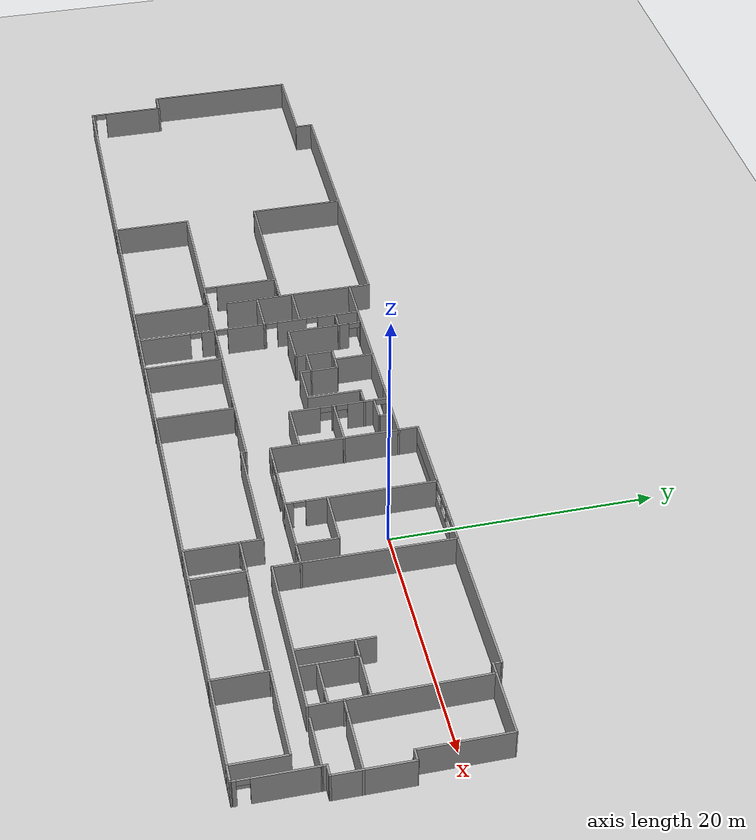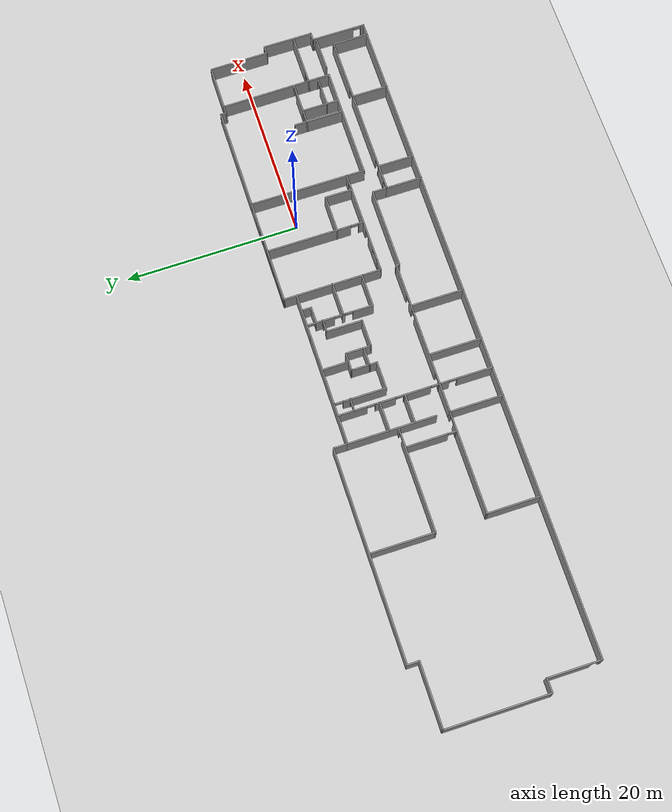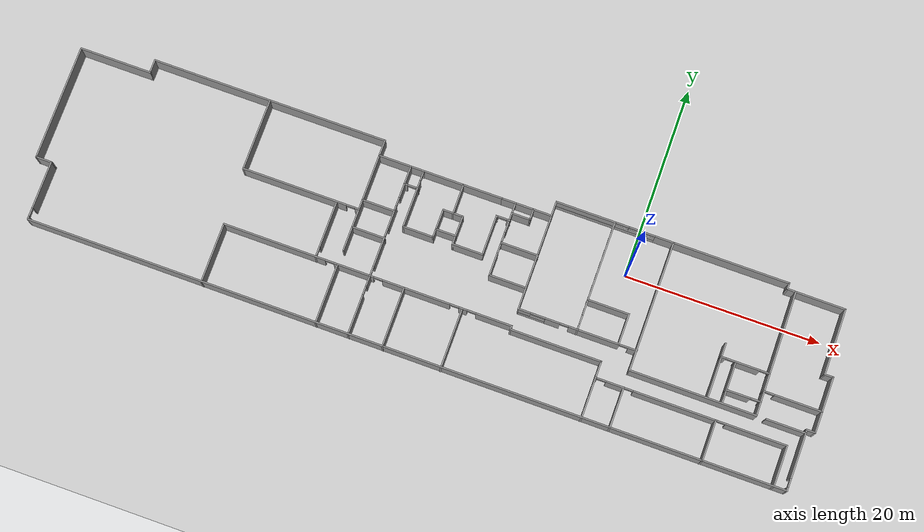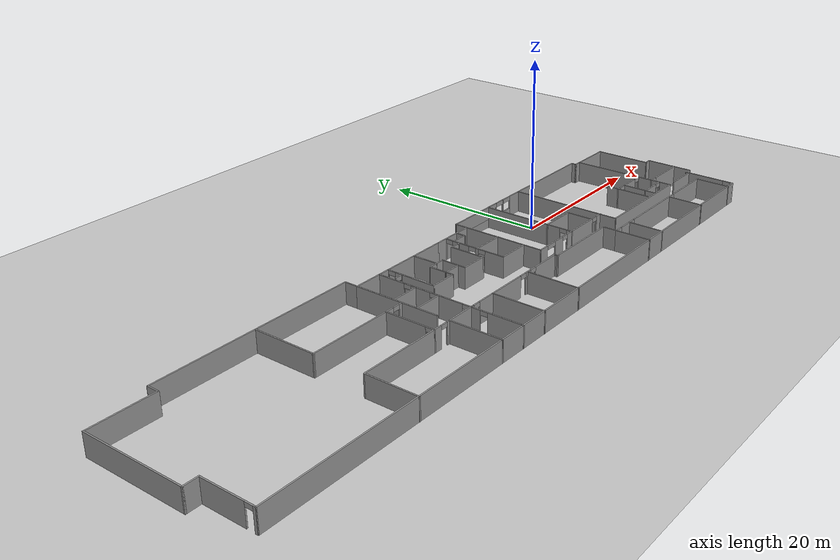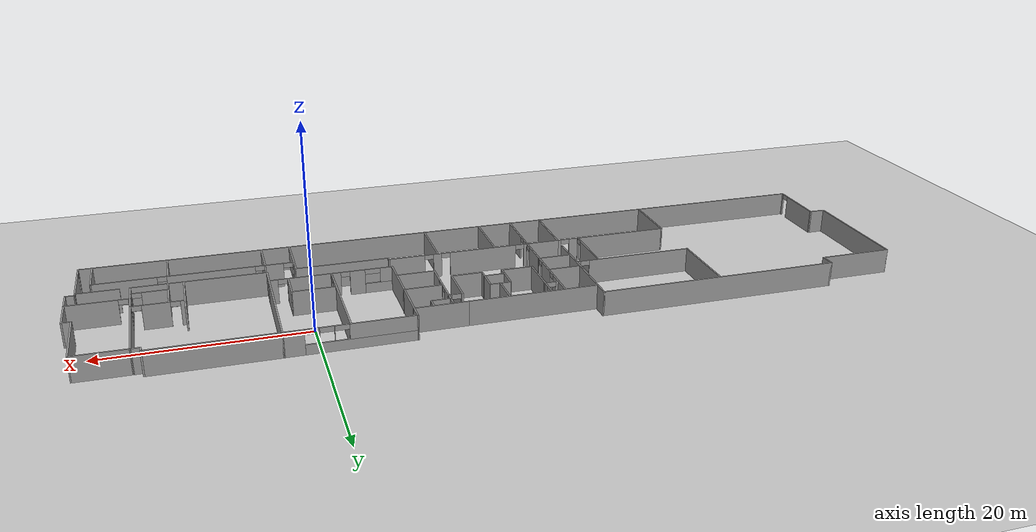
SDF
<sdf version="1.7">
 <world name="default">
  <light name="sun" type="directional">
   <pose>0 0 10 0 -0 0</pose>
   <diffuse>0.8 0.8 0.8 1</diffuse>
   <specular>0.2 0.2 0.2 1</specular>
   <attenuation>
    <range>1000</range>
    <constant>0.9</constant>
    <linear>0.01</linear>
    <quadratic>0.001</quadratic>
   </attenuation>
   <direction>-0.5 0.1 -0.9</direction>
   <spot><inner_angle>0</inner_angle><outer_angle>0</outer_angle><falloff>0</falloff></spot>
  </light>
  <model name="ground_plane">
   <static>1</static>
   <link name="link">
    <collision name="collision">
     <geometry><plane><normal>0 0 1</normal><size>100 100</size></plane></geometry>
     <surface><friction><ode><mu>100</mu><mu2>50</mu2></ode></friction></surface>
    </collision>
    <visual name="visual">
     <cast_shadows>0</cast_shadows>
     <geometry><plane><normal>0 0 1</normal><size>100 100</size></plane></geometry>
     <material>
      <script><uri>file://media/materials/scripts/gazebo.material</uri><name>Gazebo/Grey</name></script>
     </material>
    </visual>
   </link>
  </model>
  <gravity>0 0 -9.8</gravity>
  <magnetic_field>6e-06 2.3e-05 -4.2e-05</magnetic_field>
  <atmosphere type="adiabatic"/>
  <physics type="ode">
   <max_step_size>0.001</max_step_size>
   <real_time_factor>1</real_time_factor>
   <real_time_update_rate>1000</real_time_update_rate>
  </physics>
  <scene><ambient>0.4 0.4 0.4 1</ambient><background>0.7 0.7 0.7 1</background><shadows>1</shadows></scene>
  <audio><device>default</device></audio>
  <spherical_coordinates>
   <surface_model>EARTH_WGS84</surface_model>
   <latitude_deg>0</latitude_deg>
   <longitude_deg>0</longitude_deg>
   <elevation>0</elevation>
   <heading_deg>0</heading_deg>
  </spherical_coordinates>
  <model name="4th_floor_full">
   <pose>-18.2329 -5.23028 0 0 -0 3.13626</pose>
   <link name="Wall_1">
    <collision name="Wall_1_Collision">
     <geometry><box><size>13.5 0.15 2.5</size></box></geometry>
     <pose>0 0 1.25 0 -0 0</pose>
    </collision>
    <visual name="Wall_1_Visual">
     <pose>0 0 1.25 0 -0 0</pose>
     <geometry><box><size>13.5 0.15 2.5</size></box></geometry>
     <material>
      <script><uri>file://media/materials/scripts/gazebo.material</uri><name>Gazebo/Grey</name></script>
      <ambient>1 1 1 1</ambient>
     </material>
     <meta><layer>0</layer></meta>
    </visual>
    <pose>-21.539 -2.89994 0 0 -0 -1.5708</pose>
   </link>
   <link name="Wall_10">
    <pose>-15.5141 -3.90886 0 0 -0 -1.56844</pose>
    <visual name="Wall_10_Visual_0">
     <pose>-5.38184 0 1.25 0 -0 0</pose>
     <geometry><box><size>0.691437 0.15 2.5</size></box></geometry>
     <material>
      <script><uri>file://media/materials/scripts/gazebo.material</uri><name>Gazebo/Grey</name></script>
      <ambient>1 1 1 1</ambient>
     </material>
     <meta><layer>0</layer></meta>
    </visual>
    <collision name="Wall_10_Collision_0">
     <geometry><box><size>0.691437 0.15 2.5</size></box></geometry>
     <pose>-5.38184 0 1.25 0 -0 0</pose>
    </collision>
    <visual name="Wall_10_Visual_1">
     <pose>0.795718 0 1.25 0 -0 0</pose>
     <geometry><box><size>9.86368 0.15 2.5</size></box></geometry>
     <material>
      <script><uri>file://media/materials/scripts/gazebo.material</uri><name>Gazebo/Grey</name></script>
      <ambient>1 1 1 1</ambient>
     </material>
     <meta><layer>0</layer></meta>
    </visual>
    <collision name="Wall_10_Collision_1">
     <geometry><box><size>9.86368 0.15 2.5</size></box></geometry>
     <pose>0.795718 0 1.25 0 -0 0</pose>
    </collision>
    <visual name="Wall_10_Visual_2">
     <pose>-4.58612 0 2.25 0 -0 0</pose>
     <geometry><box><size>0.9 0.15 0.5</size></box></geometry>
     <material>
      <script><uri>file://media/materials/scripts/gazebo.material</uri><name>Gazebo/Grey</name></script>
      <ambient>1 1 1 1</ambient>
     </material>
     <meta><layer>0</layer></meta>
    </visual>
    <collision name="Wall_10_Collision_2">
     <geometry><box><size>0.9 0.15 0.5</size></box></geometry>
     <pose>-4.58612 0 2.25 0 -0 0</pose>
    </collision>
   </link>
   <link name="Wall_100">
    <collision name="Wall_100_Collision">
     <geometry><box><size>1.18449 0.15 2.5</size></box></geometry>
     <pose>0 0 1.25 0 -0 0</pose>
    </collision>
    <visual name="Wall_100_Visual">
     <pose>0 0 1.25 0 -0 0</pose>
     <geometry><box><size>1.18449 0.15 2.5</size></box></geometry>
     <material>
      <script><uri>file://media/materials/scripts/gazebo.material</uri><name>Gazebo/Grey</name></script>
      <ambient>1 1 1 1</ambient>
     </material>
     <meta><layer>0</layer></meta>
    </visual>
    <pose>0.19827 -5.05997 0 0 -0 0.005985</pose>
   </link>
   <link name="Wall_101">
    <collision name="Wall_101_Collision">
     <geometry><box><size>2.2151 0.15 2.5</size></box></geometry>
     <pose>0 0 1.25 0 -0 0</pose>
    </collision>
    <visual name="Wall_101_Visual">
     <pose>0 0 1.25 0 -0 0</pose>
     <geometry><box><size>2.2151 0.15 2.5</size></box></geometry>
     <material>
      <script><uri>file://media/materials/scripts/gazebo.material</uri><name>Gazebo/Grey</name></script>
      <ambient>1 1 1 1</ambient>
     </material>
     <meta><layer>0</layer></meta>
    </visual>
    <pose>0.72251 -4.02435 0 0 -0 1.56402</pose>
   </link>
   <link name="Wall_103">
    <collision name="Wall_103_Collision">
     <geometry><box><size>1.14162 0.15 2.5</size></box></geometry>
     <pose>0 0 1.25 0 -0 0</pose>
    </collision>
    <visual name="Wall_103_Visual">
     <pose>0 0 1.25 0 -0 0</pose>
     <geometry><box><size>1.14162 0.15 2.5</size></box></geometry>
     <material>
      <script><uri>file://media/materials/scripts/gazebo.material</uri><name>Gazebo/Grey</name></script>
      <ambient>1 1 1 1</ambient>
     </material>
     <meta><layer>0</layer></meta>
    </visual>
    <pose>-0.814774 -5.05997 0 0 -0 3.13535</pose>
   </link>
   <link name="Wall_104">
    <collision name="Wall_104_Collision">
     <geometry><box><size>2.21041 0.15 2.5</size></box></geometry>
     <pose>0 0 1.25 0 -0 0</pose>
    </collision>
    <visual name="Wall_104_Visual">
     <pose>0 0 1.25 0 -0 0</pose>
     <geometry><box><size>2.21041 0.15 2.5</size></box></geometry>
     <material>
      <script><uri>file://media/materials/scripts/gazebo.material</uri><name>Gazebo/Grey</name></script>
      <ambient>1 1 1 1</ambient>
     </material>
     <meta><layer>0</layer></meta>
    </visual>
    <pose>-1.305 -4.02668 0 0 -0 1.56538</pose>
   </link>
   <link name="Wall_106">
    <collision name="Wall_106_Collision">
     <geometry><box><size>7.5 0.15 2.5</size></box></geometry>
     <pose>0 0 1.25 0 -0 0</pose>
    </collision>
    <visual name="Wall_106_Visual">
     <pose>0 0 1.25 0 -0 0</pose>
     <geometry><box><size>7.5 0.15 2.5</size></box></geometry>
     <material>
      <script><uri>file://media/materials/scripts/gazebo.material</uri><name>Gazebo/Grey</name></script>
      <ambient>1 1 1 1</ambient>
     </material>
     <meta><layer>0</layer></meta>
    </visual>
    <pose>20.6058 -5.98067 0 0 -0 1.5708</pose>
   </link>
   <link name="Wall_108">
    <pose>14.5558 -2.30567 0 0 -0 3.14159</pose>
    <visual name="Wall_108_Visual_0">
     <pose>-0.69819 0 1.25 0 -0 0</pose>
     <geometry><box><size>10.8536 0.15 2.5</size></box></geometry>
     <material>
      <script><uri>file://media/materials/scripts/gazebo.material</uri><name>Gazebo/Grey</name></script>
      <ambient>1 1 1 1</ambient>
     </material>
     <meta><layer>0</layer></meta>
    </visual>
    <collision name="Wall_108_Collision_0">
     <geometry><box><size>10.8536 0.15 2.5</size></box></geometry>
     <pose>-0.69819 0 1.25 0 -0 0</pose>
    </collision>
    <visual name="Wall_108_Visual_1">
     <pose>5.87681 0 1.25 0 -0 0</pose>
     <geometry><box><size>0.496381 0.15 2.5</size></box></geometry>
     <material>
      <script><uri>file://media/materials/scripts/gazebo.material</uri><name>Gazebo/Grey</name></script>
      <ambient>1 1 1 1</ambient>
     </material>
     <meta><layer>0</layer></meta>
    </visual>
    <collision name="Wall_108_Collision_1">
     <geometry><box><size>0.496381 0.15 2.5</size></box></geometry>
     <pose>5.87681 0 1.25 0 -0 0</pose>
    </collision>
    <visual name="Wall_108_Visual_2">
     <pose>5.17862 0 2.25 0 -0 0</pose>
     <geometry><box><size>0.9 0.15 0.5</size></box></geometry>
     <material>
      <script><uri>file://media/materials/scripts/gazebo.material</uri><name>Gazebo/Grey</name></script>
      <ambient>1 1 1 1</ambient>
     </material>
     <meta><layer>0</layer></meta>
    </visual>
    <collision name="Wall_108_Collision_2">
     <geometry><box><size>0.9 0.15 0.5</size></box></geometry>
     <pose>5.17862 0 2.25 0 -0 0</pose>
    </collision>
   </link>
   <link name="Wall_110">
    <collision name="Wall_110_Collision">
     <geometry><box><size>12 0.15 2.5</size></box></geometry>
     <pose>0 0 1.25 0 -0 0</pose>
    </collision>
    <visual name="Wall_110_Visual">
     <pose>0 0 1.25 0 -0 0</pose>
     <geometry><box><size>12 0.15 2.5</size></box></geometry>
     <material>
      <script><uri>file://media/materials/scripts/gazebo.material</uri><name>Gazebo/Grey</name></script>
      <ambient>1 1 1 1</ambient>
     </material>
     <meta><layer>0</layer></meta>
    </visual>
    <pose>40.1925 -2.41314 0 0 -0 1.5708</pose>
   </link>
   <link name="Wall_111">
    <collision name="Wall_111_Collision">
     <geometry><box><size>1.75 0.15 2.5</size></box></geometry>
     <pose>0 0 1.25 0 -0 0</pose>
    </collision>
    <visual name="Wall_111_Visual">
     <pose>0 0 1.25 0 -0 0</pose>
     <geometry><box><size>1.75 0.15 2.5</size></box></geometry>
     <material>
      <script><uri>file://media/materials/scripts/gazebo.material</uri><name>Gazebo/Grey</name></script>
      <ambient>1 1 1 1</ambient>
     </material>
     <meta><layer>0</layer></meta>
    </visual>
    <pose>39.3925 3.51186 0 0 -0 3.14159</pose>
   </link>
   <link name="Wall_113">
    <pose>38.5925 6.56186 0 0 -0 1.5708</pose>
    <visual name="Wall_113_Visual_0">
     <pose>-0.629068 0 1.25 0 -0 0</pose>
     <geometry><box><size>4.99186 0.15 2.5</size></box></geometry>
     <material>
      <script><uri>file://media/materials/scripts/gazebo.material</uri><name>Gazebo/Grey</name></script>
      <ambient>1 1 1 1</ambient>
     </material>
     <meta><layer>0</layer></meta>
    </visual>
    <collision name="Wall_113_Collision_0">
     <geometry><box><size>4.99186 0.15 2.5</size></box></geometry>
     <pose>-0.629068 0 1.25 0 -0 0</pose>
    </collision>
    <visual name="Wall_113_Visual_1">
     <pose>2.94593 0 1.25 0 -0 0</pose>
     <geometry><box><size>0.358137 0.15 2.5</size></box></geometry>
     <material>
      <script><uri>file://media/materials/scripts/gazebo.material</uri><name>Gazebo/Grey</name></script>
      <ambient>1 1 1 1</ambient>
     </material>
     <meta><layer>0</layer></meta>
    </visual>
    <collision name="Wall_113_Collision_1">
     <geometry><box><size>0.358137 0.15 2.5</size></box></geometry>
     <pose>2.94593 0 1.25 0 -0 0</pose>
    </collision>
    <visual name="Wall_113_Visual_2">
     <pose>2.31686 0 2.25 0 -0 0</pose>
     <geometry><box><size>0.9 0.15 0.5</size></box></geometry>
     <material>
      <script><uri>file://media/materials/scripts/gazebo.material</uri><name>Gazebo/Grey</name></script>
      <ambient>1 1 1 1</ambient>
     </material>
     <meta><layer>0</layer></meta>
    </visual>
    <collision name="Wall_113_Collision_2">
     <geometry><box><size>0.9 0.15 0.5</size></box></geometry>
     <pose>2.31686 0 2.25 0 -0 0</pose>
    </collision>
   </link>
   <link name="Wall_115">
    <pose>-39.3473 6.73743 0 0 -0 1.5708</pose>
    <visual name="Wall_115_Visual_0">
     <pose>-0.669517 0 1.25 0 -0 0</pose>
     <geometry><box><size>4.66097 0.15 2.5</size></box></geometry>
     <material>
      <script><uri>file://media/materials/scripts/gazebo.material</uri><name>Gazebo/Grey</name></script>
      <ambient>1 1 1 1</ambient>
     </material>
     <meta><layer>0</layer></meta>
    </visual>
    <collision name="Wall_115_Collision_0">
     <geometry><box><size>4.66097 0.15 2.5</size></box></geometry>
     <pose>-0.669517 0 1.25 0 -0 0</pose>
    </collision>
    <visual name="Wall_115_Visual_1">
     <pose>2.78048 0 1.25 0 -0 0</pose>
     <geometry><box><size>0.439034 0.15 2.5</size></box></geometry>
     <material>
      <script><uri>file://media/materials/scripts/gazebo.material</uri><name>Gazebo/Grey</name></script>
      <ambient>1 1 1 1</ambient>
     </material>
     <meta><layer>0</layer></meta>
    </visual>
    <collision name="Wall_115_Collision_1">
     <geometry><box><size>0.439034 0.15 2.5</size></box></geometry>
     <pose>2.78048 0 1.25 0 -0 0</pose>
    </collision>
    <visual name="Wall_115_Visual_2">
     <pose>2.11097 0 2.25 0 -0 0</pose>
     <geometry><box><size>0.9 0.15 0.5</size></box></geometry>
     <material>
      <script><uri>file://media/materials/scripts/gazebo.material</uri><name>Gazebo/Grey</name></script>
      <ambient>1 1 1 1</ambient>
     </material>
     <meta><layer>0</layer></meta>
    </visual>
    <collision name="Wall_115_Collision_2">
     <geometry><box><size>0.9 0.15 0.5</size></box></geometry>
     <pose>2.11097 0 2.25 0 -0 0</pose>
    </collision>
   </link>
   <link name="Wall_117">
    <collision name="Wall_117_Collision">
     <geometry><box><size>78.0898 0.15 2.5</size></box></geometry>
     <pose>0 0 1.25 0 -0 0</pose>
    </collision>
    <visual name="Wall_117_Visual">
     <pose>0 0 1.25 0 -0 0</pose>
     <geometry><box><size>78.0898 0.15 2.5</size></box></geometry>
     <material>
      <script><uri>file://media/materials/scripts/gazebo.material</uri><name>Gazebo/Grey</name></script>
      <ambient>1 1 1 1</ambient>
     </material>
     <meta><layer>0</layer></meta>
    </visual>
    <pose>-0.377401 9.63715 0 0 -0 -0.000649</pose>
   </link>
   <link name="Wall_121">
    <pose>14.4573 3.55629 0 0 -0 0</pose>
    <visual name="Wall_121_Visual_0">
     <pose>-5.76798 0 1.25 0 -0 0</pose>
     <geometry><box><size>0.464033 0.15 2.5</size></box></geometry>
     <material>
      <script><uri>file://media/materials/scripts/gazebo.material</uri><name>Gazebo/Grey</name></script>
      <ambient>1 1 1 1</ambient>
     </material>
     <meta><layer>0</layer></meta>
    </visual>
    <collision name="Wall_121_Collision_0">
     <geometry><box><size>0.464033 0.15 2.5</size></box></geometry>
     <pose>-5.76798 0 1.25 0 -0 0</pose>
    </collision>
    <visual name="Wall_121_Visual_1">
     <pose>0.682016 0 1.25 0 -0 0</pose>
     <geometry><box><size>10.636 0.15 2.5</size></box></geometry>
     <material>
      <script><uri>file://media/materials/scripts/gazebo.material</uri><name>Gazebo/Grey</name></script>
      <ambient>1 1 1 1</ambient>
     </material>
     <meta><layer>0</layer></meta>
    </visual>
    <collision name="Wall_121_Collision_1">
     <geometry><box><size>10.636 0.15 2.5</size></box></geometry>
     <pose>0.682016 0 1.25 0 -0 0</pose>
    </collision>
    <visual name="Wall_121_Visual_2">
     <pose>-5.08597 0 2.25 0 -0 0</pose>
     <geometry><box><size>0.9 0.15 0.5</size></box></geometry>
     <material>
      <script><uri>file://media/materials/scripts/gazebo.material</uri><name>Gazebo/Grey</name></script>
      <ambient>1 1 1 1</ambient>
     </material>
     <meta><layer>0</layer></meta>
    </visual>
    <collision name="Wall_121_Collision_2">
     <geometry><box><size>0.9 0.15 0.5</size></box></geometry>
     <pose>-5.08597 0 2.25 0 -0 0</pose>
    </collision>
   </link>
   <link name="Wall_122">
    <collision name="Wall_122_Collision">
     <geometry><box><size>6.25 0.15 2.5</size></box></geometry>
     <pose>0 0 1.25 0 -0 0</pose>
    </collision>
    <visual name="Wall_122_Visual">
     <pose>0 0 1.25 0 -0 0</pose>
     <geometry><box><size>6.25 0.15 2.5</size></box></geometry>
     <material>
      <script><uri>file://media/materials/scripts/gazebo.material</uri><name>Gazebo/Grey</name></script>
      <ambient>1 1 1 1</ambient>
     </material>
     <meta><layer>0</layer></meta>
    </visual>
    <pose>20.3823 6.60629 0 0 -0 1.5708</pose>
   </link>
   <link name="Wall_127">
    <pose>10.7997 0.638877 0 0 -0 1.5708</pose>
    <visual name="Wall_127_Visual_0">
     <pose>-0.541177 0 1.25 0 -0 0</pose>
     <geometry><box><size>4.91765 0.15 2.5</size></box></geometry>
     <material>
      <script><uri>file://media/materials/scripts/gazebo.material</uri><name>Gazebo/Grey</name></script>
      <ambient>1 1 1 1</ambient>
     </material>
     <meta><layer>0</layer></meta>
    </visual>
    <collision name="Wall_127_Collision_0">
     <geometry><box><size>4.91765 0.15 2.5</size></box></geometry>
     <pose>-0.541177 0 1.25 0 -0 0</pose>
    </collision>
    <visual name="Wall_127_Visual_1">
     <pose>2.90882 0 1.25 0 -0 0</pose>
     <geometry><box><size>0.182355 0.15 2.5</size></box></geometry>
     <material>
      <script><uri>file://media/materials/scripts/gazebo.material</uri><name>Gazebo/Grey</name></script>
      <ambient>1 1 1 1</ambient>
     </material>
     <meta><layer>0</layer></meta>
    </visual>
    <collision name="Wall_127_Collision_1">
     <geometry><box><size>0.182355 0.15 2.5</size></box></geometry>
     <pose>2.90882 0 1.25 0 -0 0</pose>
    </collision>
    <visual name="Wall_127_Visual_2">
     <pose>2.36764 0 2.25 0 -0 0</pose>
     <geometry><box><size>0.9 0.15 0.5</size></box></geometry>
     <material>
      <script><uri>file://media/materials/scripts/gazebo.material</uri><name>Gazebo/Grey</name></script>
      <ambient>1 1 1 1</ambient>
     </material>
     <meta><layer>0</layer></meta>
    </visual>
    <collision name="Wall_127_Collision_2">
     <geometry><box><size>0.9 0.15 0.5</size></box></geometry>
     <pose>2.36764 0 2.25 0 -0 0</pose>
    </collision>
   </link>
   <link name="Wall_129">
    <collision name="Wall_129_Collision">
     <geometry><box><size>6.25 0.15 2.5</size></box></geometry>
     <pose>0 0 1.25 0 -0 0</pose>
    </collision>
    <visual name="Wall_129_Visual">
     <pose>0 0 1.25 0 -0 0</pose>
     <geometry><box><size>6.25 0.15 2.5</size></box></geometry>
     <material>
      <script><uri>file://media/materials/scripts/gazebo.material</uri><name>Gazebo/Grey</name></script>
      <ambient>1 1 1 1</ambient>
     </material>
     <meta><layer>0</layer></meta>
    </visual>
    <pose>8.53225 6.60629 0 0 -0 1.5708</pose>
   </link>
   <link name="Wall_131">
    <pose>5.18225 6.60629 0 0 -0 1.5708</pose>
    <visual name="Wall_131_Visual_0">
     <pose>-2.53744 0 1.25 0 -0 0</pose>
     <geometry><box><size>1.17511 0.15 2.5</size></box></geometry>
     <material>
      <script><uri>file://media/materials/scripts/gazebo.material</uri><name>Gazebo/Grey</name></script>
      <ambient>1 1 1 1</ambient>
     </material>
     <meta><layer>0</layer></meta>
    </visual>
    <collision name="Wall_131_Collision_0">
     <geometry><box><size>1.17511 0.15 2.5</size></box></geometry>
     <pose>-2.53744 0 1.25 0 -0 0</pose>
    </collision>
    <visual name="Wall_131_Visual_1">
     <pose>1.03756 0 1.25 0 -0 0</pose>
     <geometry><box><size>4.17489 0.15 2.5</size></box></geometry>
     <material>
      <script><uri>file://media/materials/scripts/gazebo.material</uri><name>Gazebo/Grey</name></script>
      <ambient>1 1 1 1</ambient>
     </material>
     <meta><layer>0</layer></meta>
    </visual>
    <collision name="Wall_131_Collision_1">
     <geometry><box><size>4.17489 0.15 2.5</size></box></geometry>
     <pose>1.03756 0 1.25 0 -0 0</pose>
    </collision>
    <visual name="Wall_131_Visual_2">
     <pose>-1.49989 0 2.25 0 -0 0</pose>
     <geometry><box><size>0.9 0.15 0.5</size></box></geometry>
     <material>
      <script><uri>file://media/materials/scripts/gazebo.material</uri><name>Gazebo/Grey</name></script>
      <ambient>1 1 1 1</ambient>
     </material>
     <meta><layer>0</layer></meta>
    </visual>
    <collision name="Wall_131_Collision_2">
     <geometry><box><size>0.9 0.15 0.5</size></box></geometry>
     <pose>-1.49989 0 2.25 0 -0 0</pose>
    </collision>
   </link>
   <link name="Wall_133">
    <collision name="Wall_133_Collision">
     <geometry><box><size>4.25 0.15 2.5</size></box></geometry>
     <pose>0 0 1.25 0 -0 0</pose>
    </collision>
    <visual name="Wall_133_Visual">
     <pose>0 0 1.25 0 -0 0</pose>
     <geometry><box><size>4.25 0.15 2.5</size></box></geometry>
     <material>
      <script><uri>file://media/materials/scripts/gazebo.material</uri><name>Gazebo/Grey</name></script>
      <ambient>1 1 1 1</ambient>
     </material>
     <meta><layer>0</layer></meta>
    </visual>
    <pose>-38.0412 7.62065 0 0 -0 -1.5708</pose>
   </link>
   <link name="Wall_134">
    <pose>-28.3662 5.57065 0 0 -0 0</pose>
    <visual name="Wall_134_Visual_0">
     <pose>-6.64062 0 1.25 0 -0 0</pose>
     <geometry><box><size>6.21875 0.15 2.5</size></box></geometry>
     <material>
      <script><uri>file://media/materials/scripts/gazebo.material</uri><name>Gazebo/Grey</name></script>
      <ambient>1 1 1 1</ambient>
     </material>
     <meta><layer>0</layer></meta>
    </visual>
    <collision name="Wall_134_Collision_0">
     <geometry><box><size>6.21875 0.15 2.5</size></box></geometry>
     <pose>-6.64062 0 1.25 0 -0 0</pose>
    </collision>
    <visual name="Wall_134_Visual_1">
     <pose>1.60609 0 1.25 0 -0 0</pose>
     <geometry><box><size>8.47467 0.15 2.5</size></box></geometry>
     <material>
      <script><uri>file://media/materials/scripts/gazebo.material</uri><name>Gazebo/Grey</name></script>
      <ambient>1 1 1 1</ambient>
     </material>
     <meta><layer>0</layer></meta>
    </visual>
    <collision name="Wall_134_Collision_1">
     <geometry><box><size>8.47467 0.15 2.5</size></box></geometry>
     <pose>1.60609 0 1.25 0 -0 0</pose>
    </collision>
    <visual name="Wall_134_Visual_2">
     <pose>7.67435 0 1.25 0 -0 0</pose>
     <geometry><box><size>1.86184 0.15 2.5</size></box></geometry>
     <material>
      <script><uri>file://media/materials/scripts/gazebo.material</uri><name>Gazebo/Grey</name></script>
      <ambient>1 1 1 1</ambient>
     </material>
     <meta><layer>0</layer></meta>
    </visual>
    <collision name="Wall_134_Collision_2">
     <geometry><box><size>1.86184 0.15 2.5</size></box></geometry>
     <pose>7.67435 0 1.25 0 -0 0</pose>
    </collision>
    <visual name="Wall_134_Visual_3">
     <pose>9.62763 0 1.25 0 -0 0</pose>
     <geometry><box><size>0.244731 0.15 2.5</size></box></geometry>
     <material>
      <script><uri>file://media/materials/scripts/gazebo.material</uri><name>Gazebo/Grey</name></script>
      <ambient>1 1 1 1</ambient>
     </material>
     <meta><layer>0</layer></meta>
    </visual>
    <collision name="Wall_134_Collision_3">
     <geometry><box><size>0.244731 0.15 2.5</size></box></geometry>
     <pose>9.62763 0 1.25 0 -0 0</pose>
    </collision>
    <visual name="Wall_134_Visual_4">
     <pose>-3.08125 0 2.25 0 -0 0</pose>
     <geometry><box><size>0.9 0.15 0.5</size></box></geometry>
     <material>
      <script><uri>file://media/materials/scripts/gazebo.material</uri><name>Gazebo/Grey</name></script>
      <ambient>1 1 1 1</ambient>
     </material>
     <meta><layer>0</layer></meta>
    </visual>
    <collision name="Wall_134_Collision_4">
     <geometry><box><size>0.9 0.15 0.5</size></box></geometry>
     <pose>-3.08125 0 2.25 0 -0 0</pose>
    </collision>
    <visual name="Wall_134_Visual_5">
     <pose>6.29343 0 2.25 0 -0 0</pose>
     <geometry><box><size>0.9 0.15 0.5</size></box></geometry>
     <material>
      <script><uri>file://media/materials/scripts/gazebo.material</uri><name>Gazebo/Grey</name></script>
      <ambient>1 1 1 1</ambient>
     </material>
     <meta><layer>0</layer></meta>
    </visual>
    <collision name="Wall_134_Collision_5">
     <geometry><box><size>0.9 0.15 0.5</size></box></geometry>
     <pose>6.29343 0 2.25 0 -0 0</pose>
    </collision>
    <visual name="Wall_134_Visual_6">
     <pose>9.05527 0 2.25 0 -0 0</pose>
     <geometry><box><size>0.9 0.15 0.5</size></box></geometry>
     <material>
      <script><uri>file://media/materials/scripts/gazebo.material</uri><name>Gazebo/Grey</name></script>
      <ambient>1 1 1 1</ambient>
     </material>
     <meta><layer>0</layer></meta>
    </visual>
    <collision name="Wall_134_Collision_6">
     <geometry><box><size>0.9 0.15 0.5</size></box></geometry>
     <pose>9.05527 0 2.25 0 -0 0</pose>
    </collision>
   </link>
   <link name="Wall_135">
    <collision name="Wall_135_Collision">
     <geometry><box><size>4.25 0.15 2.5</size></box></geometry>
     <pose>0 0 1.25 0 -0 0</pose>
    </collision>
    <visual name="Wall_135_Visual">
     <pose>0 0 1.25 0 -0 0</pose>
     <geometry><box><size>4.25 0.15 2.5</size></box></geometry>
     <material>
      <script><uri>file://media/materials/scripts/gazebo.material</uri><name>Gazebo/Grey</name></script>
      <ambient>1 1 1 1</ambient>
     </material>
     <meta><layer>0</layer></meta>
    </visual>
    <pose>-18.6912 7.62065 0 0 -0 1.5708</pose>
   </link>
   <link name="Wall_137">
    <collision name="Wall_137_Collision">
     <geometry><box><size>4.25 0.15 2.5</size></box></geometry>
     <pose>0 0 1.25 0 -0 0</pose>
    </collision>
    <visual name="Wall_137_Visual">
     <pose>0 0 1.25 0 -0 0</pose>
     <geometry><box><size>4.25 0.15 2.5</size></box></geometry>
     <material>
      <script><uri>file://media/materials/scripts/gazebo.material</uri><name>Gazebo/Grey</name></script>
      <ambient>1 1 1 1</ambient>
     </material>
     <meta><layer>0</layer></meta>
    </visual>
    <pose>-30.8702 7.63814 0 0 -0 -1.5708</pose>
   </link>
   <link name="Wall_139">
    <collision name="Wall_139_Collision">
     <geometry><box><size>4.25 0.15 2.5</size></box></geometry>
     <pose>0 0 1.25 0 -0 0</pose>
    </collision>
    <visual name="Wall_139_Visual">
     <pose>0 0 1.25 0 -0 0</pose>
     <geometry><box><size>4.25 0.15 2.5</size></box></geometry>
     <material>
      <script><uri>file://media/materials/scripts/gazebo.material</uri><name>Gazebo/Grey</name></script>
      <ambient>1 1 1 1</ambient>
     </material>
     <meta><layer>0</layer></meta>
    </visual>
    <pose>-21.548 7.60316 0 0 -0 -1.5708</pose>
   </link>
   <link name="Wall_14">
    <collision name="Wall_14_Collision">
     <geometry><box><size>3.25 0.15 2.5</size></box></geometry>
     <pose>0 0 1.25 0 -0 0</pose>
    </collision>
    <visual name="Wall_14_Visual">
     <pose>0 0 1.25 0 -0 0</pose>
     <geometry><box><size>3.25 0.15 2.5</size></box></geometry>
     <material>
      <script><uri>file://media/materials/scripts/gazebo.material</uri><name>Gazebo/Grey</name></script>
      <ambient>1 1 1 1</ambient>
     </material>
     <meta><layer>0</layer></meta>
    </visual>
    <pose>-19.7261 0.162934 0 0 -0 -1.5708</pose>
   </link>
   <link name="Wall_141">
    <pose>-2.11775 3.55629 0 0 -0 3.14159</pose>
    <visual name="Wall_141_Visual_0">
     <pose>-7.14407 0 1.25 0 -0 0</pose>
     <geometry><box><size>0.461854 0.15 2.5</size></box></geometry>
     <material>
      <script><uri>file://media/materials/scripts/gazebo.material</uri><name>Gazebo/Grey</name></script>
      <ambient>1 1 1 1</ambient>
     </material>
     <meta><layer>0</layer></meta>
    </visual>
    <collision name="Wall_141_Collision_0">
     <geometry><box><size>0.461854 0.15 2.5</size></box></geometry>
     <pose>-7.14407 0 1.25 0 -0 0</pose>
    </collision>
    <visual name="Wall_141_Visual_1">
     <pose>-2.51914 0 1.25 0 -0 0</pose>
     <geometry><box><size>6.98802 0.15 2.5</size></box></geometry>
     <material>
      <script><uri>file://media/materials/scripts/gazebo.material</uri><name>Gazebo/Grey</name></script>
      <ambient>1 1 1 1</ambient>
     </material>
     <meta><layer>0</layer></meta>
    </visual>
    <collision name="Wall_141_Collision_1">
     <geometry><box><size>6.98802 0.15 2.5</size></box></geometry>
     <pose>-2.51914 0 1.25 0 -0 0</pose>
    </collision>
    <visual name="Wall_141_Visual_2">
     <pose>2.29937 0 1.25 0 -0 0</pose>
     <geometry><box><size>0.849006 0.15 2.5</size></box></geometry>
     <material>
      <script><uri>file://media/materials/scripts/gazebo.material</uri><name>Gazebo/Grey</name></script>
      <ambient>1 1 1 1</ambient>
     </material>
     <meta><layer>0</layer></meta>
    </visual>
    <collision name="Wall_141_Collision_2">
     <geometry><box><size>0.849006 0.15 2.5</size></box></geometry>
     <pose>2.29937 0 1.25 0 -0 0</pose>
    </collision>
    <visual name="Wall_141_Visual_3">
     <pose>5.49944 0 1.25 0 -0 0</pose>
     <geometry><box><size>3.75112 0.15 2.5</size></box></geometry>
     <material>
      <script><uri>file://media/materials/scripts/gazebo.material</uri><name>Gazebo/Grey</name></script>
      <ambient>1 1 1 1</ambient>
     </material>
     <meta><layer>0</layer></meta>
    </visual>
    <collision name="Wall_141_Collision_3">
     <geometry><box><size>3.75112 0.15 2.5</size></box></geometry>
     <pose>5.49944 0 1.25 0 -0 0</pose>
    </collision>
    <visual name="Wall_141_Visual_4">
     <pose>-6.46315 0 2.25 0 -0 0</pose>
     <geometry><box><size>0.9 0.15 0.5</size></box></geometry>
     <material>
      <script><uri>file://media/materials/scripts/gazebo.material</uri><name>Gazebo/Grey</name></script>
      <ambient>1 1 1 1</ambient>
     </material>
     <meta><layer>0</layer></meta>
    </visual>
    <collision name="Wall_141_Collision_4">
     <geometry><box><size>0.9 0.15 0.5</size></box></geometry>
     <pose>-6.46315 0 2.25 0 -0 0</pose>
    </collision>
    <visual name="Wall_141_Visual_5">
     <pose>1.42487 0 2.25 0 -0 0</pose>
     <geometry><box><size>0.9 0.15 0.5</size></box></geometry>
     <material>
      <script><uri>file://media/materials/scripts/gazebo.material</uri><name>Gazebo/Grey</name></script>
      <ambient>1 1 1 1</ambient>
     </material>
     <meta><layer>0</layer></meta>
    </visual>
    <collision name="Wall_141_Collision_5">
     <geometry><box><size>0.9 0.15 0.5</size></box></geometry>
     <pose>1.42487 0 2.25 0 -0 0</pose>
    </collision>
    <visual name="Wall_141_Visual_6">
     <pose>3.17388 0 2.25 0 -0 0</pose>
     <geometry><box><size>0.9 0.15 0.5</size></box></geometry>
     <material>
      <script><uri>file://media/materials/scripts/gazebo.material</uri><name>Gazebo/Grey</name></script>
      <ambient>1 1 1 1</ambient>
     </material>
     <meta><layer>0</layer></meta>
    </visual>
    <collision name="Wall_141_Collision_6">
     <geometry><box><size>0.9 0.15 0.5</size></box></geometry>
     <pose>3.17388 0 2.25 0 -0 0</pose>
    </collision>
   </link>
   <link name="Wall_144">
    <collision name="Wall_144_Collision">
     <geometry><box><size>6.25 0.15 2.5</size></box></geometry>
     <pose>0 0 1.25 0 -0 0</pose>
    </collision>
    <visual name="Wall_144_Visual">
     <pose>0 0 1.25 0 -0 0</pose>
     <geometry><box><size>6.25 0.15 2.5</size></box></geometry>
     <material>
      <script><uri>file://media/materials/scripts/gazebo.material</uri><name>Gazebo/Grey</name></script>
      <ambient>1 1 1 1</ambient>
     </material>
     <meta><layer>0</layer></meta>
    </visual>
    <pose>-4.36465 6.62819 0 0 -0 -1.5708</pose>
   </link>
   <link name="Wall_146">
    <collision name="Wall_146_Collision">
     <geometry><box><size>6.25 0.15 2.5</size></box></geometry>
     <pose>0 0 1.25 0 -0 0</pose>
    </collision>
    <visual name="Wall_146_Visual">
     <pose>0 0 1.25 0 -0 0</pose>
     <geometry><box><size>6.25 0.15 2.5</size></box></geometry>
     <material>
      <script><uri>file://media/materials/scripts/gazebo.material</uri><name>Gazebo/Grey</name></script>
      <ambient>1 1 1 1</ambient>
     </material>
     <meta><layer>0</layer></meta>
    </visual>
    <pose>1.65193 6.61069 0 0 -0 -1.5708</pose>
   </link>
   <link name="Wall_15">
    <collision name="Wall_15_Collision">
     <geometry><box><size>4.37001 0.15 2.5</size></box></geometry>
     <pose>0 0 1.25 0 -0 0</pose>
    </collision>
    <visual name="Wall_15_Visual">
     <pose>0 0 1.25 0 -0 0</pose>
     <geometry><box><size>4.37001 0.15 2.5</size></box></geometry>
     <material>
      <script><uri>file://media/materials/scripts/gazebo.material</uri><name>Gazebo/Grey</name></script>
      <ambient>1 1 1 1</ambient>
     </material>
     <meta><layer>0</layer></meta>
    </visual>
    <pose>-17.6161 -1.39207 0 0 -0 -0.00237</pose>
   </link>
   <link name="Wall_151">
    <collision name="Wall_151_Collision">
     <geometry><box><size>0.5 0.15 2.5</size></box></geometry>
     <pose>0 0 1.25 0 -0 0</pose>
    </collision>
    <visual name="Wall_151_Visual">
     <pose>0 0 1.25 0 -0 0</pose>
     <geometry><box><size>0.5 0.15 2.5</size></box></geometry>
     <material>
      <script><uri>file://media/materials/scripts/gazebo.material</uri><name>Gazebo/Grey</name></script>
      <ambient>1 1 1 1</ambient>
     </material>
     <meta><layer>0</layer></meta>
    </visual>
    <pose>-9.41775 3.73129 0 0 -0 1.5708</pose>
   </link>
   <link name="Wall_153">
    <collision name="Wall_153_Collision">
     <geometry><box><size>9.4 0.15 2.5</size></box></geometry>
     <pose>0 0 1.25 0 -0 0</pose>
    </collision>
    <visual name="Wall_153_Visual">
     <pose>0 0 1.25 0 -0 0</pose>
     <geometry><box><size>9.4 0.15 2.5</size></box></geometry>
     <material>
      <script><uri>file://media/materials/scripts/gazebo.material</uri><name>Gazebo/Grey</name></script>
      <ambient>1 1 1 1</ambient>
     </material>
     <meta><layer>0</layer></meta>
    </visual>
    <pose>-14.0427 3.90629 0 0 -0 3.14159</pose>
   </link>
   <link name="Wall_155">
    <collision name="Wall_155_Collision">
     <geometry><box><size>1.8 0.15 2.5</size></box></geometry>
     <pose>0 0 1.25 0 -0 0</pose>
    </collision>
    <visual name="Wall_155_Visual">
     <pose>0 0 1.25 0 -0 0</pose>
     <geometry><box><size>1.8 0.15 2.5</size></box></geometry>
     <material>
      <script><uri>file://media/materials/scripts/gazebo.material</uri><name>Gazebo/Grey</name></script>
      <ambient>1 1 1 1</ambient>
     </material>
     <meta><layer>0</layer></meta>
    </visual>
    <pose>-18.6912 4.74565 0 0 -0 -1.5708</pose>
   </link>
   <link name="Wall_17">
    <collision name="Wall_17_Collision">
     <geometry><box><size>12 0.15 2.5</size></box></geometry>
     <pose>0 0 1.25 0 -0 0</pose>
    </collision>
    <visual name="Wall_17_Visual">
     <pose>0 0 1.25 0 -0 0</pose>
     <geometry><box><size>12 0.15 2.5</size></box></geometry>
     <material>
      <script><uri>file://media/materials/scripts/gazebo.material</uri><name>Gazebo/Grey</name></script>
      <ambient>1 1 1 1</ambient>
     </material>
     <meta><layer>0</layer></meta>
    </visual>
    <pose>-27.464 -9.57493 0 0 -0 3.14159</pose>
   </link>
   <link name="Wall_18">
    <collision name="Wall_18_Collision">
     <geometry><box><size>0.75 0.15 2.5</size></box></geometry>
     <pose>0 0 1.25 0 -0 0</pose>
    </collision>
    <visual name="Wall_18_Visual">
     <pose>0 0 1.25 0 -0 0</pose>
     <geometry><box><size>0.75 0.15 2.5</size></box></geometry>
     <material>
      <script><uri>file://media/materials/scripts/gazebo.material</uri><name>Gazebo/Grey</name></script>
      <ambient>1 1 1 1</ambient>
     </material>
     <meta><layer>0</layer></meta>
    </visual>
    <pose>-33.389 -9.27494 0 0 -0 1.5708</pose>
   </link>
   <link name="Wall_19">
    <collision name="Wall_19_Collision">
     <geometry><box><size>1 0.15 2.5</size></box></geometry>
     <pose>0 0 1.25 0 -0 0</pose>
    </collision>
    <visual name="Wall_19_Visual">
     <pose>0 0 1.25 0 -0 0</pose>
     <geometry><box><size>1 0.15 2.5</size></box></geometry>
     <material>
      <script><uri>file://media/materials/scripts/gazebo.material</uri><name>Gazebo/Grey</name></script>
      <ambient>1 1 1 1</ambient>
     </material>
     <meta><layer>0</layer></meta>
    </visual>
    <pose>-33.814 -8.97494 0 0 -0 3.14159</pose>
   </link>
   <link name="Wall_21">
    <collision name="Wall_21_Collision">
     <geometry><box><size>12.9196 0.15 2.5</size></box></geometry>
     <pose>0 0 1.25 0 -0 0</pose>
    </collision>
    <visual name="Wall_21_Visual">
     <pose>0 0 1.25 0 -0 0</pose>
     <geometry><box><size>12.9196 0.15 2.5</size></box></geometry>
     <material>
      <script><uri>file://media/materials/scripts/gazebo.material</uri><name>Gazebo/Grey</name></script>
      <ambient>1 1 1 1</ambient>
     </material>
     <meta><layer>0</layer></meta>
    </visual>
    <pose>-34.311 -2.5905 0 0 -0 1.58207</pose>
   </link>
   <link name="Wall_24">
    <collision name="Wall_24_Collision">
     <geometry><box><size>13 0.15 2.5</size></box></geometry>
     <pose>0 0 1.25 0 -0 0</pose>
    </collision>
    <visual name="Wall_24_Visual">
     <pose>0 0 1.25 0 -0 0</pose>
     <geometry><box><size>13 0.15 2.5</size></box></geometry>
     <material>
      <script><uri>file://media/materials/scripts/gazebo.material</uri><name>Gazebo/Grey</name></script>
      <ambient>1 1 1 1</ambient>
     </material>
     <meta><layer>0</layer></meta>
    </visual>
    <pose>-27.964 3.78836 0 0 -0 3.13952</pose>
   </link>
   <link name="Wall_26">
    <collision name="Wall_26_Collision">
     <geometry><box><size>5.75 0.15 2.5</size></box></geometry>
     <pose>0 0 1.25 0 -0 0</pose>
    </collision>
    <visual name="Wall_26_Visual">
     <pose>0 0 1.25 0 -0 0</pose>
     <geometry><box><size>5.75 0.15 2.5</size></box></geometry>
     <material>
      <script><uri>file://media/materials/scripts/gazebo.material</uri><name>Gazebo/Grey</name></script>
      <ambient>1 1 1 1</ambient>
     </material>
     <meta><layer>0</layer></meta>
    </visual>
    <pose>-29.4417 0.940476 0 0 -0 -1.5708</pose>
   </link>
   <link name="Wall_28">
    <pose>-31.8667 -0.478299 0 0 -0 3.14159</pose>
    <visual name="Wall_28_Visual_0">
     <pose>-2.24009 0 1.25 0 -0 0</pose>
     <geometry><box><size>0.519822 0.15 2.5</size></box></geometry>
     <material>
      <script><uri>file://media/materials/scripts/gazebo.material</uri><name>Gazebo/Grey</name></script>
      <ambient>1 1 1 1</ambient>
     </material>
     <meta><layer>0</layer></meta>
    </visual>
    <collision name="Wall_28_Collision_0">
     <geometry><box><size>0.519822 0.15 2.5</size></box></geometry>
     <pose>-2.24009 0 1.25 0 -0 0</pose>
    </collision>
    <visual name="Wall_28_Visual_1">
     <pose>0.200571 0 1.25 0 -0 0</pose>
     <geometry><box><size>2.5615 0.15 2.5</size></box></geometry>
     <material>
      <script><uri>file://media/materials/scripts/gazebo.material</uri><name>Gazebo/Grey</name></script>
      <ambient>1 1 1 1</ambient>
     </material>
     <meta><layer>0</layer></meta>
    </visual>
    <collision name="Wall_28_Collision_1">
     <geometry><box><size>2.5615 0.15 2.5</size></box></geometry>
     <pose>0.200571 0 1.25 0 -0 0</pose>
    </collision>
    <visual name="Wall_28_Visual_2">
     <pose>2.44066 0 1.25 0 -0 0</pose>
     <geometry><box><size>0.11868 0.15 2.5</size></box></geometry>
     <material>
      <script><uri>file://media/materials/scripts/gazebo.material</uri><name>Gazebo/Grey</name></script>
      <ambient>1 1 1 1</ambient>
     </material>
     <meta><layer>0</layer></meta>
    </visual>
    <collision name="Wall_28_Collision_2">
     <geometry><box><size>0.11868 0.15 2.5</size></box></geometry>
     <pose>2.44066 0 1.25 0 -0 0</pose>
    </collision>
    <visual name="Wall_28_Visual_3">
     <pose>-1.53018 0 2.25 0 -0 0</pose>
     <geometry><box><size>0.9 0.15 0.5</size></box></geometry>
     <material>
      <script><uri>file://media/materials/scripts/gazebo.material</uri><name>Gazebo/Grey</name></script>
      <ambient>1 1 1 1</ambient>
     </material>
     <meta><layer>0</layer></meta>
    </visual>
    <collision name="Wall_28_Collision_3">
     <geometry><box><size>0.9 0.15 0.5</size></box></geometry>
     <pose>-1.53018 0 2.25 0 -0 0</pose>
    </collision>
    <visual name="Wall_28_Visual_4">
     <pose>1.93132 0 2.25 0 -0 0</pose>
     <geometry><box><size>0.9 0.15 0.5</size></box></geometry>
     <material>
      <script><uri>file://media/materials/scripts/gazebo.material</uri><name>Gazebo/Grey</name></script>
      <ambient>1 1 1 1</ambient>
     </material>
     <meta><layer>0</layer></meta>
    </visual>
    <collision name="Wall_28_Collision_4">
     <geometry><box><size>0.9 0.15 0.5</size></box></geometry>
     <pose>1.93132 0 2.25 0 -0 0</pose>
    </collision>
   </link>
   <link name="Wall_3">
    <pose>-15.489 -9.57493 0 0 -0 0</pose>
    <visual name="Wall_3_Visual_0">
     <pose>-5.13864 0 1.25 0 -0 0</pose>
     <geometry><box><size>1.97271 0.15 2.5</size></box></geometry>
     <material>
      <script><uri>file://media/materials/scripts/gazebo.material</uri><name>Gazebo/Grey</name></script>
      <ambient>1 1 1 1</ambient>
     </material>
     <meta><layer>0</layer></meta>
    </visual>
    <collision name="Wall_3_Collision_0">
     <geometry><box><size>1.97271 0.15 2.5</size></box></geometry>
     <pose>-5.13864 0 1.25 0 -0 0</pose>
    </collision>
    <visual name="Wall_3_Visual_1">
     <pose>0.986356 0 0.5 0 -0 0</pose>
     <geometry><box><size>10.2773 0.15 1</size></box></geometry>
     <material>
      <script><uri>file://media/materials/scripts/gazebo.material</uri><name>Gazebo/Grey</name></script>
      <ambient>1 1 1 1</ambient>
     </material>
     <meta><layer>0</layer></meta>
    </visual>
    <collision name="Wall_3_Collision_1">
     <geometry><box><size>10.2773 0.15 1</size></box></geometry>
     <pose>0.986356 0 0.5 0 -0 0</pose>
    </collision>
    <visual name="Wall_3_Visual_2">
     <pose>-2.82748 0 1.75 0 -0 0</pose>
     <geometry><box><size>0.049615 0.15 1.5</size></box></geometry>
     <material>
      <script><uri>file://media/materials/scripts/gazebo.material</uri><name>Gazebo/Grey</name></script>
      <ambient>1 1 1 1</ambient>
     </material>
     <meta><layer>0</layer></meta>
    </visual>
    <collision name="Wall_3_Collision_2">
     <geometry><box><size>0.049615 0.15 1.5</size></box></geometry>
     <pose>-2.82748 0 1.75 0 -0 0</pose>
    </collision>
    <visual name="Wall_3_Visual_3">
     <pose>-1.48163 0 1.75 0 -0 0</pose>
     <geometry><box><size>0.042094 0.15 1.5</size></box></geometry>
     <material>
      <script><uri>file://media/materials/scripts/gazebo.material</uri><name>Gazebo/Grey</name></script>
      <ambient>1 1 1 1</ambient>
     </material>
     <meta><layer>0</layer></meta>
    </visual>
    <collision name="Wall_3_Collision_3">
     <geometry><box><size>0.042094 0.15 1.5</size></box></geometry>
     <pose>-1.48163 0 1.75 0 -0 0</pose>
    </collision>
    <visual name="Wall_3_Visual_4">
     <pose>2.98221 0 1.75 0 -0 0</pose>
     <geometry><box><size>6.28558 0.15 1.5</size></box></geometry>
     <material>
      <script><uri>file://media/materials/scripts/gazebo.material</uri><name>Gazebo/Grey</name></script>
      <ambient>1 1 1 1</ambient>
     </material>
     <meta><layer>0</layer></meta>
    </visual>
    <collision name="Wall_3_Collision_4">
     <geometry><box><size>6.28558 0.15 1.5</size></box></geometry>
     <pose>2.98221 0 1.75 0 -0 0</pose>
    </collision>
    <visual name="Wall_3_Visual_5">
     <pose>-3.50229 0 2.25 0 -0 0</pose>
     <geometry><box><size>1.3 0.15 0.5</size></box></geometry>
     <material>
      <script><uri>file://media/materials/scripts/gazebo.material</uri><name>Gazebo/Grey</name></script>
      <ambient>1 1 1 1</ambient>
     </material>
     <meta><layer>0</layer></meta>
    </visual>
    <collision name="Wall_3_Collision_5">
     <geometry><box><size>1.3 0.15 0.5</size></box></geometry>
     <pose>-3.50229 0 2.25 0 -0 0</pose>
    </collision>
    <visual name="Wall_3_Visual_6">
     <pose>-2.15267 0 2.25 0 -0 0</pose>
     <geometry><box><size>1.3 0.15 0.5</size></box></geometry>
     <material>
      <script><uri>file://media/materials/scripts/gazebo.material</uri><name>Gazebo/Grey</name></script>
      <ambient>1 1 1 1</ambient>
     </material>
     <meta><layer>0</layer></meta>
    </visual>
    <collision name="Wall_3_Collision_6">
     <geometry><box><size>1.3 0.15 0.5</size></box></geometry>
     <pose>-2.15267 0 2.25 0 -0 0</pose>
    </collision>
    <visual name="Wall_3_Visual_7">
     <pose>-0.810579 0 2.25 0 -0 0</pose>
     <geometry><box><size>1.3 0.15 0.5</size></box></geometry>
     <material>
      <script><uri>file://media/materials/scripts/gazebo.material</uri><name>Gazebo/Grey</name></script>
      <ambient>1 1 1 1</ambient>
     </material>
     <meta><layer>0</layer></meta>
    </visual>
    <collision name="Wall_3_Collision_7">
     <geometry><box><size>1.3 0.15 0.5</size></box></geometry>
     <pose>-0.810579 0 2.25 0 -0 0</pose>
    </collision>
   </link>
   <link name="Wall_31">
    <collision name="Wall_31_Collision">
     <geometry><box><size>4.359 0.15 2.5</size></box></geometry>
     <pose>0 0 1.25 0 -0 0</pose>
    </collision>
    <visual name="Wall_31_Visual">
     <pose>0 0 1.25 0 -0 0</pose>
     <geometry><box><size>4.359 0.15 2.5</size></box></geometry>
     <material>
      <script><uri>file://media/materials/scripts/gazebo.material</uri><name>Gazebo/Grey</name></script>
      <ambient>1 1 1 1</ambient>
     </material>
     <meta><layer>0</layer></meta>
    </visual>
    <pose>-30.9115 1.65388 0 0 -0 1.5708</pose>
   </link>
   <link name="Wall_33">
    <pose>-32.6365 2.41288 0 0 -0 -3.13493</pose>
    <visual name="Wall_33_Visual_0">
     <pose>-0.544858 0 1.25 0 -0 0</pose>
     <geometry><box><size>2.51036 0.15 2.5</size></box></geometry>
     <material>
      <script><uri>file://media/materials/scripts/gazebo.material</uri><name>Gazebo/Grey</name></script>
      <ambient>1 1 1 1</ambient>
     </material>
     <meta><layer>0</layer></meta>
    </visual>
    <collision name="Wall_33_Collision_0">
     <geometry><box><size>2.51036 0.15 2.5</size></box></geometry>
     <pose>-0.544858 0 1.25 0 -0 0</pose>
    </collision>
    <visual name="Wall_33_Visual_1">
     <pose>1.70518 0 1.25 0 -0 0</pose>
     <geometry><box><size>0.189715 0.15 2.5</size></box></geometry>
     <material>
      <script><uri>file://media/materials/scripts/gazebo.material</uri><name>Gazebo/Grey</name></script>
      <ambient>1 1 1 1</ambient>
     </material>
     <meta><layer>0</layer></meta>
    </visual>
    <collision name="Wall_33_Collision_1">
     <geometry><box><size>0.189715 0.15 2.5</size></box></geometry>
     <pose>1.70518 0 1.25 0 -0 0</pose>
    </collision>
    <visual name="Wall_33_Visual_2">
     <pose>1.16032 0 2.25 0 -0 0</pose>
     <geometry><box><size>0.9 0.15 0.5</size></box></geometry>
     <material>
      <script><uri>file://media/materials/scripts/gazebo.material</uri><name>Gazebo/Grey</name></script>
      <ambient>1 1 1 1</ambient>
     </material>
     <meta><layer>0</layer></meta>
    </visual>
    <collision name="Wall_33_Collision_2">
     <geometry><box><size>0.9 0.15 0.5</size></box></geometry>
     <pose>1.16032 0 2.25 0 -0 0</pose>
    </collision>
   </link>
   <link name="Wall_35">
    <collision name="Wall_35_Collision">
     <geometry><box><size>5.2 0.15 2.5</size></box></geometry>
     <pose>0 0 1.25 0 -0 0</pose>
    </collision>
    <visual name="Wall_35_Visual">
     <pose>0 0 1.25 0 -0 0</pose>
     <geometry><box><size>5.2 0.15 2.5</size></box></geometry>
     <material>
      <script><uri>file://media/materials/scripts/gazebo.material</uri><name>Gazebo/Grey</name></script>
      <ambient>1 1 1 1</ambient>
     </material>
     <meta><layer>0</layer></meta>
    </visual>
    <pose>-36.764 -8.96566 0 0 -0 3.13792</pose>
   </link>
   <link name="Wall_40">
    <collision name="Wall_40_Collision">
     <geometry><box><size>6.88713 0.15 2.5</size></box></geometry>
     <pose>0 0 1.25 0 -0 0</pose>
    </collision>
    <visual name="Wall_40_Visual">
     <pose>0 0 1.25 0 -0 0</pose>
     <geometry><box><size>6.88713 0.15 2.5</size></box></geometry>
     <material>
      <script><uri>file://media/materials/scripts/gazebo.material</uri><name>Gazebo/Grey</name></script>
      <ambient>1 1 1 1</ambient>
     </material>
     <meta><layer>0</layer></meta>
    </visual>
    <pose>-39.3122 -5.58825 0 0 -0 1.57769</pose>
   </link>
   <link name="Wall_41">
    <collision name="Wall_41_Collision">
     <geometry><box><size>1 0.15 2.5</size></box></geometry>
     <pose>0 0 1.25 0 -0 0</pose>
    </collision>
    <visual name="Wall_41_Visual">
     <pose>0 0 1.25 0 -0 0</pose>
     <geometry><box><size>1 0.15 2.5</size></box></geometry>
     <material>
      <script><uri>file://media/materials/scripts/gazebo.material</uri><name>Gazebo/Grey</name></script>
      <ambient>1 1 1 1</ambient>
     </material>
     <meta><layer>0</layer></meta>
    </visual>
    <pose>-39.7604 -2.22011 0 0 -0 3.14159</pose>
   </link>
   <link name="Wall_43">
    <collision name="Wall_43_Collision">
     <geometry><box><size>5.83342 0.15 2.5</size></box></geometry>
     <pose>0 0 1.25 0 -0 0</pose>
    </collision>
    <visual name="Wall_43_Visual">
     <pose>0 0 1.25 0 -0 0</pose>
     <geometry><box><size>5.83342 0.15 2.5</size></box></geometry>
     <material>
      <script><uri>file://media/materials/scripts/gazebo.material</uri><name>Gazebo/Grey</name></script>
      <ambient>1 1 1 1</ambient>
     </material>
     <meta><layer>0</layer></meta>
    </visual>
    <pose>-40.1883 0.621187 0 0 -0 1.5718</pose>
   </link>
   <link name="Wall_44">
    <collision name="Wall_44_Collision">
     <geometry><box><size>1 0.15 2.5</size></box></geometry>
     <pose>0 0 1.25 0 -0 0</pose>
    </collision>
    <visual name="Wall_44_Visual">
     <pose>0 0 1.25 0 -0 0</pose>
     <geometry><box><size>1 0.15 2.5</size></box></geometry>
     <material>
      <script><uri>file://media/materials/scripts/gazebo.material</uri><name>Gazebo/Grey</name></script>
      <ambient>1 1 1 1</ambient>
     </material>
     <meta><layer>0</layer></meta>
    </visual>
    <pose>-39.7662 3.46248 0 0 -0 0</pose>
   </link>
   <link name="Wall_47">
    <collision name="Wall_47_Collision">
     <geometry><box><size>0.5 0.15 2.5</size></box></geometry>
     <pose>0 0 1.25 0 -0 0</pose>
    </collision>
    <visual name="Wall_47_Visual">
     <pose>0 0 1.25 0 -0 0</pose>
     <geometry><box><size>0.5 0.15 2.5</size></box></geometry>
     <material>
      <script><uri>file://media/materials/scripts/gazebo.material</uri><name>Gazebo/Grey</name></script>
      <ambient>1 1 1 1</ambient>
     </material>
     <meta><layer>0</layer></meta>
    </visual>
    <pose>-39.3442 3.63746 0 0 -0 1.58829</pose>
   </link>
   <link name="Wall_49">
    <collision name="Wall_49_Collision">
     <geometry><box><size>4.1 0.15 2.5</size></box></geometry>
     <pose>0 0 1.25 0 -0 0</pose>
    </collision>
    <visual name="Wall_49_Visual">
     <pose>0 0 1.25 0 -0 0</pose>
     <geometry><box><size>4.1 0.15 2.5</size></box></geometry>
     <material>
      <script><uri>file://media/materials/scripts/gazebo.material</uri><name>Gazebo/Grey</name></script>
      <ambient>1 1 1 1</ambient>
     </material>
     <meta><layer>0</layer></meta>
    </visual>
    <pose>-37.3723 3.81243 0 0 -0 0</pose>
   </link>
   <link name="Wall_53">
    <pose>-37.2675 1.31425 0 0 -0 0</pose>
    <visual name="Wall_53_Visual_0">
     <pose>-0.5725 0 1.25 0 -0 0</pose>
     <geometry><box><size>4.855 0.15 2.5</size></box></geometry>
     <material>
      <script><uri>file://media/materials/scripts/gazebo.material</uri><name>Gazebo/Grey</name></script>
      <ambient>1 1 1 1</ambient>
     </material>
     <meta><layer>0</layer></meta>
    </visual>
    <collision name="Wall_53_Collision_0">
     <geometry><box><size>4.855 0.15 2.5</size></box></geometry>
     <pose>-0.5725 0 1.25 0 -0 0</pose>
    </collision>
    <visual name="Wall_53_Visual_1">
     <pose>2.8775 0 1.25 0 -0 0</pose>
     <geometry><box><size>0.245 0.15 2.5</size></box></geometry>
     <material>
      <script><uri>file://media/materials/scripts/gazebo.material</uri><name>Gazebo/Grey</name></script>
      <ambient>1 1 1 1</ambient>
     </material>
     <meta><layer>0</layer></meta>
    </visual>
    <collision name="Wall_53_Collision_1">
     <geometry><box><size>0.245 0.15 2.5</size></box></geometry>
     <pose>2.8775 0 1.25 0 -0 0</pose>
    </collision>
    <visual name="Wall_53_Visual_2">
     <pose>2.305 0 2.25 0 -0 0</pose>
     <geometry><box><size>0.9 0.15 0.5</size></box></geometry>
     <material>
      <script><uri>file://media/materials/scripts/gazebo.material</uri><name>Gazebo/Grey</name></script>
      <ambient>1 1 1 1</ambient>
     </material>
     <meta><layer>0</layer></meta>
    </visual>
    <collision name="Wall_53_Collision_2">
     <geometry><box><size>0.9 0.15 0.5</size></box></geometry>
     <pose>2.305 0 2.25 0 -0 0</pose>
    </collision>
   </link>
   <link name="Wall_55">
    <collision name="Wall_55_Collision">
     <geometry><box><size>5.25 0.15 2.5</size></box></geometry>
     <pose>0 0 1.25 0 -0 0</pose>
    </collision>
    <visual name="Wall_55_Visual">
     <pose>0 0 1.25 0 -0 0</pose>
     <geometry><box><size>5.25 0.15 2.5</size></box></geometry>
     <material>
      <script><uri>file://media/materials/scripts/gazebo.material</uri><name>Gazebo/Grey</name></script>
      <ambient>1 1 1 1</ambient>
     </material>
     <meta><layer>0</layer></meta>
    </visual>
    <pose>-6.90753 -8.08814 0 0 -0 0</pose>
   </link>
   <link name="Wall_57">
    <collision name="Wall_57_Collision">
     <geometry><box><size>3.9 0.15 2.5</size></box></geometry>
     <pose>0 0 1.25 0 -0 0</pose>
    </collision>
    <visual name="Wall_57_Visual">
     <pose>0 0 1.25 0 -0 0</pose>
     <geometry><box><size>3.9 0.15 2.5</size></box></geometry>
     <material>
      <script><uri>file://media/materials/scripts/gazebo.material</uri><name>Gazebo/Grey</name></script>
      <ambient>1 1 1 1</ambient>
     </material>
     <meta><layer>0</layer></meta>
    </visual>
    <pose>-7.59195 -0.457568 0 0 -0 0</pose>
   </link>
   <link name="Wall_59">
    <pose>-5.71695 -4.25757 0 0 -0 -1.5708</pose>
    <visual name="Wall_59_Visual_0">
     <pose>-2.66556 0 1.25 0 -0 0</pose>
     <geometry><box><size>2.41888 0.15 2.5</size></box></geometry>
     <material>
      <script><uri>file://media/materials/scripts/gazebo.material</uri><name>Gazebo/Grey</name></script>
      <ambient>1 1 1 1</ambient>
     </material>
     <meta><layer>0</layer></meta>
    </visual>
    <collision name="Wall_59_Collision_0">
     <geometry><box><size>2.41888 0.15 2.5</size></box></geometry>
     <pose>-2.66556 0 1.25 0 -0 0</pose>
    </collision>
    <visual name="Wall_59_Visual_1">
     <pose>-0.386122 0 1.25 0 -0 0</pose>
     <geometry><box><size>0.34 0.15 2.5</size></box></geometry>
     <material>
      <script><uri>file://media/materials/scripts/gazebo.material</uri><name>Gazebo/Grey</name></script>
      <ambient>1 1 1 1</ambient>
     </material>
     <meta><layer>0</layer></meta>
    </visual>
    <collision name="Wall_59_Collision_1">
     <geometry><box><size>0.34 0.15 2.5</size></box></geometry>
     <pose>-0.386122 0 1.25 0 -0 0</pose>
    </collision>
    <visual name="Wall_59_Visual_2">
     <pose>1.76276 0 1.25 0 -0 0</pose>
     <geometry><box><size>2.15776 0.15 2.5</size></box></geometry>
     <material>
      <script><uri>file://media/materials/scripts/gazebo.material</uri><name>Gazebo/Grey</name></script>
      <ambient>1 1 1 1</ambient>
     </material>
     <meta><layer>0</layer></meta>
    </visual>
    <collision name="Wall_59_Collision_2">
     <geometry><box><size>2.15776 0.15 2.5</size></box></geometry>
     <pose>1.76276 0 1.25 0 -0 0</pose>
    </collision>
    <visual name="Wall_59_Visual_3">
     <pose>3.80832 0 1.25 0 -0 0</pose>
     <geometry><box><size>0.13336 0.15 2.5</size></box></geometry>
     <material>
      <script><uri>file://media/materials/scripts/gazebo.material</uri><name>Gazebo/Grey</name></script>
      <ambient>1 1 1 1</ambient>
     </material>
     <meta><layer>0</layer></meta>
    </visual>
    <collision name="Wall_59_Collision_3">
     <geometry><box><size>0.13336 0.15 2.5</size></box></geometry>
     <pose>3.80832 0 1.25 0 -0 0</pose>
    </collision>
    <visual name="Wall_59_Visual_4">
     <pose>-1.00612 0 2.25 0 -0 0</pose>
     <geometry><box><size>0.9 0.15 0.5</size></box></geometry>
     <material>
      <script><uri>file://media/materials/scripts/gazebo.material</uri><name>Gazebo/Grey</name></script>
      <ambient>1 1 1 1</ambient>
     </material>
     <meta><layer>0</layer></meta>
    </visual>
    <collision name="Wall_59_Collision_4">
     <geometry><box><size>0.9 0.15 0.5</size></box></geometry>
     <pose>-1.00612 0 2.25 0 -0 0</pose>
    </collision>
    <visual name="Wall_59_Visual_5">
     <pose>0.233878 0 2.25 0 -0 0</pose>
     <geometry><box><size>0.9 0.15 0.5</size></box></geometry>
     <material>
      <script><uri>file://media/materials/scripts/gazebo.material</uri><name>Gazebo/Grey</name></script>
      <ambient>1 1 1 1</ambient>
     </material>
     <meta><layer>0</layer></meta>
    </visual>
    <collision name="Wall_59_Collision_5">
     <geometry><box><size>0.9 0.15 0.5</size></box></geometry>
     <pose>0.233878 0 2.25 0 -0 0</pose>
    </collision>
    <visual name="Wall_59_Visual_6">
     <pose>3.29164 0 2.25 0 -0 0</pose>
     <geometry><box><size>0.9 0.15 0.5</size></box></geometry>
     <material>
      <script><uri>file://media/materials/scripts/gazebo.material</uri><name>Gazebo/Grey</name></script>
      <ambient>1 1 1 1</ambient>
     </material>
     <meta><layer>0</layer></meta>
    </visual>
    <collision name="Wall_59_Collision_6">
     <geometry><box><size>0.9 0.15 0.5</size></box></geometry>
     <pose>3.29164 0 2.25 0 -0 0</pose>
    </collision>
   </link>
   <link name="Wall_6">
    <pose>-15.529 1.73247 0 0 -0 0</pose>
    <visual name="Wall_6_Visual_0">
     <pose>-5.65421 0 1.25 0 -0 0</pose>
     <geometry><box><size>0.941588 0.15 2.5</size></box></geometry>
     <material>
      <script><uri>file://media/materials/scripts/gazebo.material</uri><name>Gazebo/Grey</name></script>
      <ambient>1 1 1 1</ambient>
     </material>
     <meta><layer>0</layer></meta>
    </visual>
    <collision name="Wall_6_Collision_0">
     <geometry><box><size>0.941588 0.15 2.5</size></box></geometry>
     <pose>-5.65421 0 1.25 0 -0 0</pose>
    </collision>
    <visual name="Wall_6_Visual_1">
     <pose>-1.68523 0 1.25 0 -0 0</pose>
     <geometry><box><size>5.19637 0.15 2.5</size></box></geometry>
     <material>
      <script><uri>file://media/materials/scripts/gazebo.material</uri><name>Gazebo/Grey</name></script>
      <ambient>1 1 1 1</ambient>
     </material>
     <meta><layer>0</layer></meta>
    </visual>
    <collision name="Wall_6_Collision_1">
     <geometry><box><size>5.19637 0.15 2.5</size></box></geometry>
     <pose>-1.68523 0 1.25 0 -0 0</pose>
    </collision>
    <visual name="Wall_6_Visual_2">
     <pose>2.55893 0 1.25 0 -0 0</pose>
     <geometry><box><size>1.49195 0.15 2.5</size></box></geometry>
     <material>
      <script><uri>file://media/materials/scripts/gazebo.material</uri><name>Gazebo/Grey</name></script>
      <ambient>1 1 1 1</ambient>
     </material>
     <meta><layer>0</layer></meta>
    </visual>
    <collision name="Wall_6_Collision_2">
     <geometry><box><size>1.49195 0.15 2.5</size></box></geometry>
     <pose>2.55893 0 1.25 0 -0 0</pose>
    </collision>
    <visual name="Wall_6_Visual_3">
     <pose>4.71495 0 0.5 0 -0 0</pose>
     <geometry><box><size>2.82009 0.15 1</size></box></geometry>
     <material>
      <script><uri>file://media/materials/scripts/gazebo.material</uri><name>Gazebo/Grey</name></script>
      <ambient>1 1 1 1</ambient>
     </material>
     <meta><layer>0</layer></meta>
    </visual>
    <collision name="Wall_6_Collision_3">
     <geometry><box><size>2.82009 0.15 1</size></box></geometry>
     <pose>4.71495 0 0.5 0 -0 0</pose>
    </collision>
    <visual name="Wall_6_Visual_4">
     <pose>5.46495 0 1.75 0 -0 0</pose>
     <geometry><box><size>1.32009 0.15 1.5</size></box></geometry>
     <material>
      <script><uri>file://media/materials/scripts/gazebo.material</uri><name>Gazebo/Grey</name></script>
      <ambient>1 1 1 1</ambient>
     </material>
     <meta><layer>0</layer></meta>
    </visual>
    <collision name="Wall_6_Collision_4">
     <geometry><box><size>1.32009 0.15 1.5</size></box></geometry>
     <pose>5.46495 0 1.75 0 -0 0</pose>
    </collision>
    <visual name="Wall_6_Visual_5">
     <pose>-4.73341 0 2.25 0 -0 0</pose>
     <geometry><box><size>0.9 0.15 0.5</size></box></geometry>
     <material>
      <script><uri>file://media/materials/scripts/gazebo.material</uri><name>Gazebo/Grey</name></script>
      <ambient>1 1 1 1</ambient>
     </material>
     <meta><layer>0</layer></meta>
    </visual>
    <collision name="Wall_6_Collision_5">
     <geometry><box><size>0.9 0.15 0.5</size></box></geometry>
     <pose>-4.73341 0 2.25 0 -0 0</pose>
    </collision>
    <visual name="Wall_6_Visual_6">
     <pose>1.36296 0 2.25 0 -0 0</pose>
     <geometry><box><size>0.9 0.15 0.5</size></box></geometry>
     <material>
      <script><uri>file://media/materials/scripts/gazebo.material</uri><name>Gazebo/Grey</name></script>
      <ambient>1 1 1 1</ambient>
     </material>
     <meta><layer>0</layer></meta>
    </visual>
    <collision name="Wall_6_Collision_6">
     <geometry><box><size>0.9 0.15 0.5</size></box></geometry>
     <pose>1.36296 0 2.25 0 -0 0</pose>
    </collision>
    <visual name="Wall_6_Visual_7">
     <pose>4.05491 0 2.25 0 -0 0</pose>
     <geometry><box><size>1.5 0.15 0.5</size></box></geometry>
     <material>
      <script><uri>file://media/materials/scripts/gazebo.material</uri><name>Gazebo/Grey</name></script>
      <ambient>1 1 1 1</ambient>
     </material>
     <meta><layer>0</layer></meta>
    </visual>
    <collision name="Wall_6_Collision_7">
     <geometry><box><size>1.5 0.15 0.5</size></box></geometry>
     <pose>4.05491 0 2.25 0 -0 0</pose>
    </collision>
   </link>
   <link name="Wall_61">
    <collision name="Wall_61_Collision">
     <geometry><box><size>3.9 0.15 2.5</size></box></geometry>
     <pose>0 0 1.25 0 -0 0</pose>
    </collision>
    <visual name="Wall_61_Visual">
     <pose>0 0 1.25 0 -0 0</pose>
     <geometry><box><size>3.9 0.15 2.5</size></box></geometry>
     <material>
      <script><uri>file://media/materials/scripts/gazebo.material</uri><name>Gazebo/Grey</name></script>
      <ambient>1 1 1 1</ambient>
     </material>
     <meta><layer>0</layer></meta>
    </visual>
    <pose>-7.62447 -3.87984 0 0 -0 0</pose>
   </link>
   <link name="Wall_63">
    <collision name="Wall_63_Collision">
     <geometry><box><size>2 0.15 2.5</size></box></geometry>
     <pose>0 0 1.25 0 -0 0</pose>
    </collision>
    <visual name="Wall_63_Visual">
     <pose>0 0 1.25 0 -0 0</pose>
     <geometry><box><size>2 0.15 2.5</size></box></geometry>
     <material>
      <script><uri>file://media/materials/scripts/gazebo.material</uri><name>Gazebo/Grey</name></script>
      <ambient>1 1 1 1</ambient>
     </material>
     <meta><layer>0</layer></meta>
    </visual>
    <pose>-6.66703 -7.00979 0 0 -0 3.14159</pose>
   </link>
   <link name="Wall_64">
    <collision name="Wall_64_Collision">
     <geometry><box><size>1.19005 0.15 2.5</size></box></geometry>
     <pose>0 0 1.25 0 -0 0</pose>
    </collision>
    <visual name="Wall_64_Visual">
     <pose>0 0 1.25 0 -0 0</pose>
     <geometry><box><size>1.19005 0.15 2.5</size></box></geometry>
     <material>
      <script><uri>file://media/materials/scripts/gazebo.material</uri><name>Gazebo/Grey</name></script>
      <ambient>1 1 1 1</ambient>
     </material>
     <meta><layer>0</layer></meta>
    </visual>
    <pose>-7.58703 -7.52979 0 0 -0 -1.56118</pose>
   </link>
   <link name="Wall_66">
    <pose>-5.07442 -6.2465 0 0 -0 0</pose>
    <visual name="Wall_66_Visual_0">
     <pose>-0.564886 0 1.25 0 -0 0</pose>
     <geometry><box><size>0.370229 0.15 2.5</size></box></geometry>
     <material>
      <script><uri>file://media/materials/scripts/gazebo.material</uri><name>Gazebo/Grey</name></script>
      <ambient>1 1 1 1</ambient>
     </material>
     <meta><layer>0</layer></meta>
    </visual>
    <collision name="Wall_66_Collision_0">
     <geometry><box><size>0.370229 0.15 2.5</size></box></geometry>
     <pose>-0.564886 0 1.25 0 -0 0</pose>
    </collision>
    <visual name="Wall_66_Visual_1">
     <pose>0.635114 0 1.25 0 -0 0</pose>
     <geometry><box><size>0.229771 0.15 2.5</size></box></geometry>
     <material>
      <script><uri>file://media/materials/scripts/gazebo.material</uri><name>Gazebo/Grey</name></script>
      <ambient>1 1 1 1</ambient>
     </material>
     <meta><layer>0</layer></meta>
    </visual>
    <collision name="Wall_66_Collision_1">
     <geometry><box><size>0.229771 0.15 2.5</size></box></geometry>
     <pose>0.635114 0 1.25 0 -0 0</pose>
    </collision>
    <visual name="Wall_66_Visual_2">
     <pose>0.070229 0 2.25 0 -0 0</pose>
     <geometry><box><size>0.9 0.15 0.5</size></box></geometry>
     <material>
      <script><uri>file://media/materials/scripts/gazebo.material</uri><name>Gazebo/Grey</name></script>
      <ambient>1 1 1 1</ambient>
     </material>
     <meta><layer>0</layer></meta>
    </visual>
    <collision name="Wall_66_Collision_2">
     <geometry><box><size>0.9 0.15 0.5</size></box></geometry>
     <pose>0.070229 0 2.25 0 -0 0</pose>
    </collision>
   </link>
   <link name="Wall_67">
    <collision name="Wall_67_Collision">
     <geometry><box><size>4.25 0.15 2.5</size></box></geometry>
     <pose>0 0 1.25 0 -0 0</pose>
    </collision>
    <visual name="Wall_67_Visual">
     <pose>0 0 1.25 0 -0 0</pose>
     <geometry><box><size>4.25 0.15 2.5</size></box></geometry>
     <material>
      <script><uri>file://media/materials/scripts/gazebo.material</uri><name>Gazebo/Grey</name></script>
      <ambient>1 1 1 1</ambient>
     </material>
     <meta><layer>0</layer></meta>
    </visual>
    <pose>-4.39942 -4.1965 0 0 -0 1.5708</pose>
   </link>
   <link name="Wall_68">
    <collision name="Wall_68_Collision">
     <geometry><box><size>3.25 0.15 2.5</size></box></geometry>
     <pose>0 0 1.25 0 -0 0</pose>
    </collision>
    <visual name="Wall_68_Visual">
     <pose>0 0 1.25 0 -0 0</pose>
     <geometry><box><size>3.25 0.15 2.5</size></box></geometry>
     <material>
      <script><uri>file://media/materials/scripts/gazebo.material</uri><name>Gazebo/Grey</name></script>
      <ambient>1 1 1 1</ambient>
     </material>
     <meta><layer>0</layer></meta>
    </visual>
    <pose>-2.84942 -2.1465 0 0 -0 0</pose>
   </link>
   <link name="Wall_69">
    <collision name="Wall_69_Collision">
     <geometry><box><size>1 0.15 2.5</size></box></geometry>
     <pose>0 0 1.25 0 -0 0</pose>
    </collision>
    <visual name="Wall_69_Visual">
     <pose>0 0 1.25 0 -0 0</pose>
     <geometry><box><size>1 0.15 2.5</size></box></geometry>
     <material>
      <script><uri>file://media/materials/scripts/gazebo.material</uri><name>Gazebo/Grey</name></script>
      <ambient>1 1 1 1</ambient>
     </material>
     <meta><layer>0</layer></meta>
    </visual>
    <pose>-1.29942 -2.5715 0 0 -0 -1.5708</pose>
   </link>
   <link name="Wall_7">
    <collision name="Wall_7_Collision">
     <geometry><box><size>11.4575 0.15 2.5</size></box></geometry>
     <pose>0 0 1.25 0 -0 0</pose>
    </collision>
    <visual name="Wall_7_Visual">
     <pose>0 0 1.25 0 -0 0</pose>
     <geometry><box><size>11.4575 0.15 2.5</size></box></geometry>
     <material>
      <script><uri>file://media/materials/scripts/gazebo.material</uri><name>Gazebo/Grey</name></script>
      <ambient>1 1 1 1</ambient>
     </material>
     <meta><layer>0</layer></meta>
    </visual>
    <pose>-9.45902 -3.92123 0 0 -0 -1.56726</pose>
   </link>
   <link name="Wall_70">
    <collision name="Wall_70_Collision">
     <geometry><box><size>2.17934 0.15 2.5</size></box></geometry>
     <pose>0 0 1.25 0 -0 0</pose>
    </collision>
    <visual name="Wall_70_Visual">
     <pose>0 0 1.25 0 -0 0</pose>
     <geometry><box><size>2.17934 0.15 2.5</size></box></geometry>
     <material>
      <script><uri>file://media/materials/scripts/gazebo.material</uri><name>Gazebo/Grey</name></script>
      <ambient>1 1 1 1</ambient>
     </material>
     <meta><layer>0</layer></meta>
    </visual>
    <pose>-0.284956 -2.99416 0 0 -0 0.002303</pose>
   </link>
   <link name="Wall_71">
    <collision name="Wall_71_Collision">
     <geometry><box><size>1 0.15 2.5</size></box></geometry>
     <pose>0 0 1.25 0 -0 0</pose>
    </collision>
    <visual name="Wall_71_Visual">
     <pose>0 0 1.25 0 -0 0</pose>
     <geometry><box><size>1 0.15 2.5</size></box></geometry>
     <material>
      <script><uri>file://media/materials/scripts/gazebo.material</uri><name>Gazebo/Grey</name></script>
      <ambient>1 1 1 1</ambient>
     </material>
     <meta><layer>0</layer></meta>
    </visual>
    <pose>0.729508 -2.56682 0 0 -0 1.5708</pose>
   </link>
   <link name="Wall_72">
    <collision name="Wall_72_Collision">
     <geometry><box><size>3.25 0.15 2.5</size></box></geometry>
     <pose>0 0 1.25 0 -0 0</pose>
    </collision>
    <visual name="Wall_72_Visual">
     <pose>0 0 1.25 0 -0 0</pose>
     <geometry><box><size>3.25 0.15 2.5</size></box></geometry>
     <material>
      <script><uri>file://media/materials/scripts/gazebo.material</uri><name>Gazebo/Grey</name></script>
      <ambient>1 1 1 1</ambient>
     </material>
     <meta><layer>0</layer></meta>
    </visual>
    <pose>2.27951 -2.14182 0 0 -0 0</pose>
   </link>
   <link name="Wall_77">
    <collision name="Wall_77_Collision">
     <geometry><box><size>13 0.15 2.5</size></box></geometry>
     <pose>0 0 1.25 0 -0 0</pose>
    </collision>
    <visual name="Wall_77_Visual">
     <pose>0 0 1.25 0 -0 0</pose>
     <geometry><box><size>13 0.15 2.5</size></box></geometry>
     <material>
      <script><uri>file://media/materials/scripts/gazebo.material</uri><name>Gazebo/Grey</name></script>
      <ambient>1 1 1 1</ambient>
     </material>
     <meta><layer>0</layer></meta>
    </visual>
    <pose>2.06747 -8.08814 0 0 -0 0</pose>
   </link>
   <link name="Wall_78">
    <collision name="Wall_78_Collision">
     <geometry><box><size>1.75 0.15 2.5</size></box></geometry>
     <pose>0 0 1.25 0 -0 0</pose>
    </collision>
    <visual name="Wall_78_Visual">
     <pose>0 0 1.25 0 -0 0</pose>
     <geometry><box><size>1.75 0.15 2.5</size></box></geometry>
     <material>
      <script><uri>file://media/materials/scripts/gazebo.material</uri><name>Gazebo/Grey</name></script>
      <ambient>1 1 1 1</ambient>
     </material>
     <meta><layer>0</layer></meta>
    </visual>
    <pose>8.49247 -8.88814 0 0 -0 -1.5708</pose>
   </link>
   <link name="Wall_80">
    <pose>3.82951 -5.06682 0 0 -0 -1.5708</pose>
    <visual name="Wall_80_Visual_0">
     <pose>-0.504881 0 1.25 0 -0 0</pose>
     <geometry><box><size>4.99024 0.15 2.5</size></box></geometry>
     <material>
      <script><uri>file://media/materials/scripts/gazebo.material</uri><name>Gazebo/Grey</name></script>
      <ambient>1 1 1 1</ambient>
     </material>
     <meta><layer>0</layer></meta>
    </visual>
    <collision name="Wall_80_Collision_0">
     <geometry><box><size>4.99024 0.15 2.5</size></box></geometry>
     <pose>-0.504881 0 1.25 0 -0 0</pose>
    </collision>
    <visual name="Wall_80_Visual_1">
     <pose>2.94512 0 1.25 0 -0 0</pose>
     <geometry><box><size>0.109763 0.15 2.5</size></box></geometry>
     <material>
      <script><uri>file://media/materials/scripts/gazebo.material</uri><name>Gazebo/Grey</name></script>
      <ambient>1 1 1 1</ambient>
     </material>
     <meta><layer>0</layer></meta>
    </visual>
    <collision name="Wall_80_Collision_1">
     <geometry><box><size>0.109763 0.15 2.5</size></box></geometry>
     <pose>2.94512 0 1.25 0 -0 0</pose>
    </collision>
    <visual name="Wall_80_Visual_2">
     <pose>2.44024 0 2.25 0 -0 0</pose>
     <geometry><box><size>0.9 0.15 0.5</size></box></geometry>
     <material>
      <script><uri>file://media/materials/scripts/gazebo.material</uri><name>Gazebo/Grey</name></script>
      <ambient>1 1 1 1</ambient>
     </material>
     <meta><layer>0</layer></meta>
    </visual>
    <collision name="Wall_80_Collision_2">
     <geometry><box><size>0.9 0.15 0.5</size></box></geometry>
     <pose>2.44024 0 2.25 0 -0 0</pose>
    </collision>
   </link>
   <link name="Wall_82">
    <collision name="Wall_82_Collision">
     <geometry><box><size>24.5 0.15 2.5</size></box></geometry>
     <pose>0 0 1.25 0 -0 0</pose>
    </collision>
    <visual name="Wall_82_Visual">
     <pose>0 0 1.25 0 -0 0</pose>
     <geometry><box><size>24.5 0.15 2.5</size></box></geometry>
     <material>
      <script><uri>file://media/materials/scripts/gazebo.material</uri><name>Gazebo/Grey</name></script>
      <ambient>1 1 1 1</ambient>
     </material>
     <meta><layer>0</layer></meta>
    </visual>
    <pose>20.6675 -9.68814 0 0 -0 0</pose>
   </link>
   <link name="Wall_83">
    <collision name="Wall_83_Collision">
     <geometry><box><size>1.5 0.15 2.5</size></box></geometry>
     <pose>0 0 1.25 0 -0 0</pose>
    </collision>
    <visual name="Wall_83_Visual">
     <pose>0 0 1.25 0 -0 0</pose>
     <geometry><box><size>1.5 0.15 2.5</size></box></geometry>
     <material>
      <script><uri>file://media/materials/scripts/gazebo.material</uri><name>Gazebo/Grey</name></script>
      <ambient>1 1 1 1</ambient>
     </material>
     <meta><layer>0</layer></meta>
    </visual>
    <pose>32.8425 -9.01314 0 0 -0 1.5708</pose>
   </link>
   <link name="Wall_85">
    <collision name="Wall_85_Collision">
     <geometry><box><size>7.5 0.15 2.5</size></box></geometry>
     <pose>0 0 1.25 0 -0 0</pose>
    </collision>
    <visual name="Wall_85_Visual">
     <pose>0 0 1.25 0 -0 0</pose>
     <geometry><box><size>7.5 0.15 2.5</size></box></geometry>
     <material>
      <script><uri>file://media/materials/scripts/gazebo.material</uri><name>Gazebo/Grey</name></script>
      <ambient>1 1 1 1</ambient>
     </material>
     <meta><layer>0</layer></meta>
    </visual>
    <pose>36.5175 -8.33814 0 0 -0 0</pose>
   </link>
   <link name="Wall_87">
    <pose>5.18225 -2.24371 0 0 -0 1.5708</pose>
    <visual name="Wall_87_Visual_0">
     <pose>-4.19424 0 1.25 0 -0 0</pose>
     <geometry><box><size>3.36153 0.15 2.5</size></box></geometry>
     <material>
      <script><uri>file://media/materials/scripts/gazebo.material</uri><name>Gazebo/Grey</name></script>
      <ambient>1 1 1 1</ambient>
     </material>
     <meta><layer>0</layer></meta>
    </visual>
    <collision name="Wall_87_Collision_0">
     <geometry><box><size>3.36153 0.15 2.5</size></box></geometry>
     <pose>-4.19424 0 1.25 0 -0 0</pose>
    </collision>
    <visual name="Wall_87_Visual_1">
     <pose>-0.421198 0 1.25 0 -0 0</pose>
     <geometry><box><size>2.38455 0.15 2.5</size></box></geometry>
     <material>
      <script><uri>file://media/materials/scripts/gazebo.material</uri><name>Gazebo/Grey</name></script>
      <ambient>1 1 1 1</ambient>
     </material>
     <meta><layer>0</layer></meta>
    </visual>
    <collision name="Wall_87_Collision_1">
     <geometry><box><size>2.38455 0.15 2.5</size></box></geometry>
     <pose>-0.421198 0 1.25 0 -0 0</pose>
    </collision>
    <visual name="Wall_87_Visual_2">
     <pose>3.23714 0 1.25 0 -0 0</pose>
     <geometry><box><size>3.13214 0.15 2.5</size></box></geometry>
     <material>
      <script><uri>file://media/materials/scripts/gazebo.material</uri><name>Gazebo/Grey</name></script>
      <ambient>1 1 1 1</ambient>
     </material>
     <meta><layer>0</layer></meta>
    </visual>
    <collision name="Wall_87_Collision_2">
     <geometry><box><size>3.13214 0.15 2.5</size></box></geometry>
     <pose>3.23714 0 1.25 0 -0 0</pose>
    </collision>
    <visual name="Wall_87_Visual_3">
     <pose>5.78911 0 1.25 0 -0 0</pose>
     <geometry><box><size>0.171786 0.15 2.5</size></box></geometry>
     <material>
      <script><uri>file://media/materials/scripts/gazebo.material</uri><name>Gazebo/Grey</name></script>
      <ambient>1 1 1 1</ambient>
     </material>
     <meta><layer>0</layer></meta>
    </visual>
    <collision name="Wall_87_Collision_3">
     <geometry><box><size>0.171786 0.15 2.5</size></box></geometry>
     <pose>5.78911 0 1.25 0 -0 0</pose>
    </collision>
    <visual name="Wall_87_Visual_4">
     <pose>-2.06347 0 2.25 0 -0 0</pose>
     <geometry><box><size>0.9 0.15 0.5</size></box></geometry>
     <material>
      <script><uri>file://media/materials/scripts/gazebo.material</uri><name>Gazebo/Grey</name></script>
      <ambient>1 1 1 1</ambient>
     </material>
     <meta><layer>0</layer></meta>
    </visual>
    <collision name="Wall_87_Collision_4">
     <geometry><box><size>0.9 0.15 0.5</size></box></geometry>
     <pose>-2.06347 0 2.25 0 -0 0</pose>
    </collision>
    <visual name="Wall_87_Visual_5">
     <pose>1.22107 0 2.25 0 -0 0</pose>
     <geometry><box><size>0.9 0.15 0.5</size></box></geometry>
     <material>
      <script><uri>file://media/materials/scripts/gazebo.material</uri><name>Gazebo/Grey</name></script>
      <ambient>1 1 1 1</ambient>
     </material>
     <meta><layer>0</layer></meta>
    </visual>
    <collision name="Wall_87_Collision_5">
     <geometry><box><size>0.9 0.15 0.5</size></box></geometry>
     <pose>1.22107 0 2.25 0 -0 0</pose>
    </collision>
    <visual name="Wall_87_Visual_6">
     <pose>5.25321 0 2.25 0 -0 0</pose>
     <geometry><box><size>0.9 0.15 0.5</size></box></geometry>
     <material>
      <script><uri>file://media/materials/scripts/gazebo.material</uri><name>Gazebo/Grey</name></script>
      <ambient>1 1 1 1</ambient>
     </material>
     <meta><layer>0</layer></meta>
    </visual>
    <collision name="Wall_87_Collision_6">
     <geometry><box><size>0.9 0.15 0.5</size></box></geometry>
     <pose>5.25321 0 2.25 0 -0 0</pose>
    </collision>
   </link>
   <link name="Wall_88">
    <collision name="Wall_88_Collision">
     <geometry><box><size>3.5 0.15 2.5</size></box></geometry>
     <pose>0 0 1.25 0 -0 0</pose>
    </collision>
    <visual name="Wall_88_Visual">
     <pose>0 0 1.25 0 -0 0</pose>
     <geometry><box><size>3.5 0.15 2.5</size></box></geometry>
     <material>
      <script><uri>file://media/materials/scripts/gazebo.material</uri><name>Gazebo/Grey</name></script>
      <ambient>1 1 1 1</ambient>
     </material>
     <meta><layer>0</layer></meta>
    </visual>
    <pose>6.85725 3.55629 0 0 -0 0</pose>
   </link>
   <link name="Wall_90">
    <collision name="Wall_90_Collision">
     <geometry><box><size>10.25 0.15 2.5</size></box></geometry>
     <pose>0 0 1.25 0 -0 0</pose>
    </collision>
    <visual name="Wall_90_Visual">
     <pose>0 0 1.25 0 -0 0</pose>
     <geometry><box><size>10.25 0.15 2.5</size></box></geometry>
     <material>
      <script><uri>file://media/materials/scripts/gazebo.material</uri><name>Gazebo/Grey</name></script>
      <ambient>1 1 1 1</ambient>
     </material>
     <meta><layer>0</layer></meta>
    </visual>
    <pose>8.49247 -3.03814 0 0 -0 1.5708</pose>
   </link>
   <link name="Wall_92">
    <collision name="Wall_92_Collision">
     <geometry><box><size>3.4 0.15 2.5</size></box></geometry>
     <pose>0 0 1.25 0 -0 0</pose>
    </collision>
    <visual name="Wall_92_Visual">
     <pose>0 0 1.25 0 -0 0</pose>
     <geometry><box><size>3.4 0.15 2.5</size></box></geometry>
     <material>
      <script><uri>file://media/materials/scripts/gazebo.material</uri><name>Gazebo/Grey</name></script>
      <ambient>1 1 1 1</ambient>
     </material>
     <meta><layer>0</layer></meta>
    </visual>
    <pose>6.83736 -3.31256 0 0 -0 3.14159</pose>
   </link>
   <link name="Wall_94">
    <collision name="Wall_94_Collision">
     <geometry><box><size>3.4 0.15 2.5</size></box></geometry>
     <pose>0 0 1.25 0 -0 0</pose>
    </collision>
    <visual name="Wall_94_Visual">
     <pose>0 0 1.25 0 -0 0</pose>
     <geometry><box><size>3.4 0.15 2.5</size></box></geometry>
     <material>
      <script><uri>file://media/materials/scripts/gazebo.material</uri><name>Gazebo/Grey</name></script>
      <ambient>1 1 1 1</ambient>
     </material>
     <meta><layer>0</layer></meta>
    </visual>
    <pose>6.7911 -0.421238 0 0 -0 3.14159</pose>
   </link>
   <link name="Wall_96">
    <pose>4.45655 -6.22702 0 0 -0 3.14159</pose>
    <visual name="Wall_96_Visual_0">
     <pose>-0.578976 0 1.25 0 -0 0</pose>
     <geometry><box><size>0.342049 0.15 2.5</size></box></geometry>
     <material>
      <script><uri>file://media/materials/scripts/gazebo.material</uri><name>Gazebo/Grey</name></script>
      <ambient>1 1 1 1</ambient>
     </material>
     <meta><layer>0</layer></meta>
    </visual>
    <collision name="Wall_96_Collision_0">
     <geometry><box><size>0.342049 0.15 2.5</size></box></geometry>
     <pose>-0.578976 0 1.25 0 -0 0</pose>
    </collision>
    <visual name="Wall_96_Visual_1">
     <pose>0.621024 0 1.25 0 -0 0</pose>
     <geometry><box><size>0.257951 0.15 2.5</size></box></geometry>
     <material>
      <script><uri>file://media/materials/scripts/gazebo.material</uri><name>Gazebo/Grey</name></script>
      <ambient>1 1 1 1</ambient>
     </material>
     <meta><layer>0</layer></meta>
    </visual>
    <collision name="Wall_96_Collision_1">
     <geometry><box><size>0.257951 0.15 2.5</size></box></geometry>
     <pose>0.621024 0 1.25 0 -0 0</pose>
    </collision>
    <visual name="Wall_96_Visual_2">
     <pose>0.042049 0 2.25 0 -0 0</pose>
     <geometry><box><size>0.9 0.15 0.5</size></box></geometry>
     <material>
      <script><uri>file://media/materials/scripts/gazebo.material</uri><name>Gazebo/Grey</name></script>
      <ambient>1 1 1 1</ambient>
     </material>
     <meta><layer>0</layer></meta>
    </visual>
    <collision name="Wall_96_Collision_2">
     <geometry><box><size>0.9 0.15 0.5</size></box></geometry>
     <pose>0.042049 0 2.25 0 -0 0</pose>
    </collision>
   </link>
   <link name="Wall_98">
    <collision name="Wall_98_Collision">
     <geometry><box><size>3.15707 0.15 2.5</size></box></geometry>
     <pose>0 0 1.25 0 -0 0</pose>
    </collision>
    <visual name="Wall_98_Visual">
     <pose>0 0 1.25 0 -0 0</pose>
     <geometry><box><size>3.15707 0.15 2.5</size></box></geometry>
     <material>
      <script><uri>file://media/materials/scripts/gazebo.material</uri><name>Gazebo/Grey</name></script>
      <ambient>1 1 1 1</ambient>
     </material>
     <meta><layer>0</layer></meta>
    </visual>
    <pose>-0.307408 -6.56655 0 0 -0 -1.5631</pose>
   </link>
   <static>1</static>
  </model>
 </world>
</sdf>
